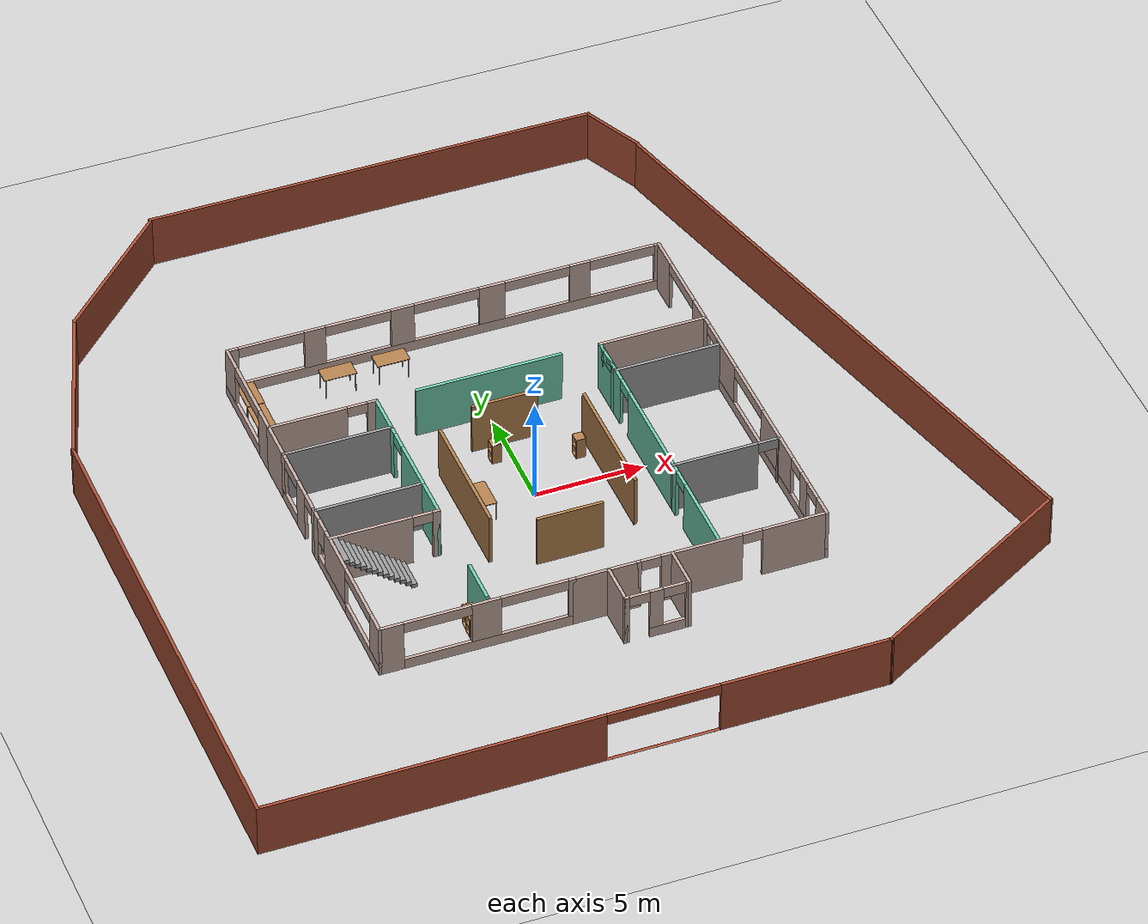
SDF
<sdf version="1.6">
 <world name="default">
  <plugin name="welcomeMessage" filename="libhello.so"/>
  <light name="sun" type="directional">
   <pose>0 0 10 0 -0 0</pose>
   <diffuse>0.8 0.8 0.8 1</diffuse>
   <specular>0.2 0.2 0.2 1</specular>
   <attenuation>
    <range>1000</range>
    <constant>0.9</constant>
    <linear>0.01</linear>
    <quadratic>0.001</quadratic>
   </attenuation>
   <direction>-0.5 0.1 -0.9</direction>
  </light>
  <model name="ground_plane">
   <static>1</static>
   <link name="link">
    <collision name="collision">
     <geometry><plane><normal>0 0 1</normal><size>100 100</size></plane></geometry>
     <surface><friction><ode><mu>100</mu><mu2>50</mu2></ode></friction></surface>
    </collision>
    <visual name="visual">
     <cast_shadows>0</cast_shadows>
     <geometry><plane><normal>0 0 1</normal><size>100 100</size></plane></geometry>
     <material>
      <script><uri>file://media/materials/scripts/gazebo.material</uri><name>Gazebo/Grey</name></script>
     </material>
    </visual>
   </link>
  </model>
  <gravity>0 0 -9.8</gravity>
  <magnetic_field>6e-06 2.3e-05 -4.2e-05</magnetic_field>
  <atmosphere type="adiabatic"/>
  <physics name="default_physics" default="0" type="ode">
   <max_step_size>0.001</max_step_size>
   <real_time_factor>1</real_time_factor>
   <real_time_update_rate>1000</real_time_update_rate>
  </physics>
  <scene><ambient>0.4 0.4 0.4 1</ambient><background>0.7 0.7 0.7 1</background><shadows>1</shadows></scene>
  <spherical_coordinates>
   <surface_model>EARTH_WGS84</surface_model>
   <latitude_deg>0</latitude_deg>
   <longitude_deg>0</longitude_deg>
   <elevation>0</elevation>
   <heading_deg>0</heading_deg>
  </spherical_coordinates>
  <model name="buildingv2">
   <pose>0.458303 2.11352 0 0 -0 0</pose>
   <link name="Stairs_1">
    <visual name="Stairs_1_Visual_0">
     <pose>-7.25739 -4.97699 0.096154 0 0 -1.5708</pose>
     <geometry><box><size>1.5 0.246923 0.192308</size></box></geometry>
     <material>
      <script><uri>file://media/materials/scripts/gazebo.material</uri><name>Gazebo/Grey</name></script>
      <ambient>1 1 1 1</ambient>
     </material>
     <meta><layer>0</layer></meta>
    </visual>
    <collision name="Stairs_1_Collision_0">
     <geometry><box><size>1.5 0.246923 0.192308</size></box></geometry>
     <pose>-7.25739 -4.97699 0.096154 0 0 -1.5708</pose>
    </collision>
    <visual name="Stairs_1_Visual_1">
     <pose>-7.50432 -4.97699 0.288462 0 0 -1.5708</pose>
     <geometry><box><size>1.5 0.246923 0.192308</size></box></geometry>
     <material>
      <script><uri>file://media/materials/scripts/gazebo.material</uri><name>Gazebo/Grey</name></script>
      <ambient>1 1 1 1</ambient>
     </material>
     <meta><layer>0</layer></meta>
    </visual>
    <collision name="Stairs_1_Collision_1">
     <geometry><box><size>1.5 0.246923 0.192308</size></box></geometry>
     <pose>-7.50432 -4.97699 0.288462 0 0 -1.5708</pose>
    </collision>
    <visual name="Stairs_1_Visual_2">
     <pose>-7.75124 -4.97699 0.480769 0 0 -1.5708</pose>
     <geometry><box><size>1.5 0.246923 0.192308</size></box></geometry>
     <material>
      <script><uri>file://media/materials/scripts/gazebo.material</uri><name>Gazebo/Grey</name></script>
      <ambient>1 1 1 1</ambient>
     </material>
     <meta><layer>0</layer></meta>
    </visual>
    <collision name="Stairs_1_Collision_2">
     <geometry><box><size>1.5 0.246923 0.192308</size></box></geometry>
     <pose>-7.75124 -4.97699 0.480769 0 0 -1.5708</pose>
    </collision>
    <visual name="Stairs_1_Visual_3">
     <pose>-7.99816 -4.97699 0.673077 0 0 -1.5708</pose>
     <geometry><box><size>1.5 0.246923 0.192308</size></box></geometry>
     <material>
      <script><uri>file://media/materials/scripts/gazebo.material</uri><name>Gazebo/Grey</name></script>
      <ambient>1 1 1 1</ambient>
     </material>
     <meta><layer>0</layer></meta>
    </visual>
    <collision name="Stairs_1_Collision_3">
     <geometry><box><size>1.5 0.246923 0.192308</size></box></geometry>
     <pose>-7.99816 -4.97699 0.673077 0 0 -1.5708</pose>
    </collision>
    <visual name="Stairs_1_Visual_4">
     <pose>-8.24509 -4.97699 0.865385 0 0 -1.5708</pose>
     <geometry><box><size>1.5 0.246923 0.192308</size></box></geometry>
     <material>
      <script><uri>file://media/materials/scripts/gazebo.material</uri><name>Gazebo/Grey</name></script>
      <ambient>1 1 1 1</ambient>
     </material>
     <meta><layer>0</layer></meta>
    </visual>
    <collision name="Stairs_1_Collision_4">
     <geometry><box><size>1.5 0.246923 0.192308</size></box></geometry>
     <pose>-8.24509 -4.97699 0.865385 0 0 -1.5708</pose>
    </collision>
    <visual name="Stairs_1_Visual_5">
     <pose>-8.49201 -4.97699 1.05769 0 0 -1.5708</pose>
     <geometry><box><size>1.5 0.246923 0.192308</size></box></geometry>
     <material>
      <script><uri>file://media/materials/scripts/gazebo.material</uri><name>Gazebo/Grey</name></script>
      <ambient>1 1 1 1</ambient>
     </material>
     <meta><layer>0</layer></meta>
    </visual>
    <collision name="Stairs_1_Collision_5">
     <geometry><box><size>1.5 0.246923 0.192308</size></box></geometry>
     <pose>-8.49201 -4.97699 1.05769 0 0 -1.5708</pose>
    </collision>
    <visual name="Stairs_1_Visual_6">
     <pose>-8.73893 -4.97699 1.25 0 0 -1.5708</pose>
     <geometry><box><size>1.5 0.246923 0.192308</size></box></geometry>
     <material>
      <script><uri>file://media/materials/scripts/gazebo.material</uri><name>Gazebo/Grey</name></script>
      <ambient>1 1 1 1</ambient>
     </material>
     <meta><layer>0</layer></meta>
    </visual>
    <collision name="Stairs_1_Collision_6">
     <geometry><box><size>1.5 0.246923 0.192308</size></box></geometry>
     <pose>-8.73893 -4.97699 1.25 0 0 -1.5708</pose>
    </collision>
    <visual name="Stairs_1_Visual_7">
     <pose>-8.98586 -4.97699 1.44231 0 0 -1.5708</pose>
     <geometry><box><size>1.5 0.246923 0.192308</size></box></geometry>
     <material>
      <script><uri>file://media/materials/scripts/gazebo.material</uri><name>Gazebo/Grey</name></script>
      <ambient>1 1 1 1</ambient>
     </material>
     <meta><layer>0</layer></meta>
    </visual>
    <collision name="Stairs_1_Collision_7">
     <geometry><box><size>1.5 0.246923 0.192308</size></box></geometry>
     <pose>-8.98586 -4.97699 1.44231 0 0 -1.5708</pose>
    </collision>
    <visual name="Stairs_1_Visual_8">
     <pose>-9.23278 -4.97699 1.63461 0 0 -1.5708</pose>
     <geometry><box><size>1.5 0.246923 0.192308</size></box></geometry>
     <material>
      <script><uri>file://media/materials/scripts/gazebo.material</uri><name>Gazebo/Grey</name></script>
      <ambient>1 1 1 1</ambient>
     </material>
     <meta><layer>0</layer></meta>
    </visual>
    <collision name="Stairs_1_Collision_8">
     <geometry><box><size>1.5 0.246923 0.192308</size></box></geometry>
     <pose>-9.23278 -4.97699 1.63461 0 0 -1.5708</pose>
    </collision>
    <visual name="Stairs_1_Visual_9">
     <pose>-9.4797 -4.97699 1.82692 0 0 -1.5708</pose>
     <geometry><box><size>1.5 0.246923 0.192308</size></box></geometry>
     <material>
      <script><uri>file://media/materials/scripts/gazebo.material</uri><name>Gazebo/Grey</name></script>
      <ambient>1 1 1 1</ambient>
     </material>
     <meta><layer>0</layer></meta>
    </visual>
    <collision name="Stairs_1_Collision_9">
     <geometry><box><size>1.5 0.246923 0.192308</size></box></geometry>
     <pose>-9.4797 -4.97699 1.82692 0 0 -1.5708</pose>
    </collision>
    <visual name="Stairs_1_Visual_10">
     <pose>-9.72662 -4.97699 2.01923 0 0 -1.5708</pose>
     <geometry><box><size>1.5 0.246923 0.192308</size></box></geometry>
     <material>
      <script><uri>file://media/materials/scripts/gazebo.material</uri><name>Gazebo/Grey</name></script>
      <ambient>1 1 1 1</ambient>
     </material>
     <meta><layer>0</layer></meta>
    </visual>
    <collision name="Stairs_1_Collision_10">
     <geometry><box><size>1.5 0.246923 0.192308</size></box></geometry>
     <pose>-9.72662 -4.97699 2.01923 0 0 -1.5708</pose>
    </collision>
    <visual name="Stairs_1_Visual_11">
     <pose>-9.97355 -4.97699 2.21154 0 0 -1.5708</pose>
     <geometry><box><size>1.5 0.246923 0.192308</size></box></geometry>
     <material>
      <script><uri>file://media/materials/scripts/gazebo.material</uri><name>Gazebo/Grey</name></script>
      <ambient>1 1 1 1</ambient>
     </material>
     <meta><layer>0</layer></meta>
    </visual>
    <collision name="Stairs_1_Collision_11">
     <geometry><box><size>1.5 0.246923 0.192308</size></box></geometry>
     <pose>-9.97355 -4.97699 2.21154 0 0 -1.5708</pose>
    </collision>
    <visual name="Stairs_1_Visual_12">
     <pose>-10.2205 -4.97699 2.40385 0 0 -1.5708</pose>
     <geometry><box><size>1.5 0.246923 0.192308</size></box></geometry>
     <material>
      <script><uri>file://media/materials/scripts/gazebo.material</uri><name>Gazebo/Grey</name></script>
      <ambient>1 1 1 1</ambient>
     </material>
     <meta><layer>0</layer></meta>
    </visual>
    <collision name="Stairs_1_Collision_12">
     <geometry><box><size>1.5 0.246923 0.192308</size></box></geometry>
     <pose>-10.2205 -4.97699 2.40385 0 0 -1.5708</pose>
    </collision>
   </link>
   <link name="Wall_102">
    <collision name="Wall_102_Collision">
     <geometry><box><size>7.5 0.15 2.5</size></box></geometry>
     <pose>0 0 1.25 0 -0 0</pose>
    </collision>
    <visual name="Wall_102_Visual">
     <pose>0 0 1.25 0 -0 0</pose>
     <geometry><box><size>7.5 0.15 2.5</size></box></geometry>
     <material>
      <script><uri>file://media/materials/scripts/gazebo.material</uri><name>Gazebo/Bricks</name></script>
      <ambient>1 1 1 1</ambient>
     </material>
     <meta><layer>0</layer></meta>
    </visual>
    <pose>-13.3137 15.568 0 0 0 -2.35619</pose>
   </link>
   <link name="Wall_103">
    <collision name="Wall_103_Collision">
     <geometry><box><size>8.52644 0.15 2.5</size></box></geometry>
     <pose>0 0 1.25 0 -0 0</pose>
    </collision>
    <visual name="Wall_103_Visual">
     <pose>0 0 1.25 0 -0 0</pose>
     <geometry><box><size>8.52644 0.15 2.5</size></box></geometry>
     <material>
      <script><uri>file://media/materials/scripts/gazebo.material</uri><name>Gazebo/Bricks</name></script>
      <ambient>1 1 1 1</ambient>
     </material>
     <meta><layer>0</layer></meta>
    </visual>
    <pose>-17.2612 9.00429 0 0 0 -1.89871</pose>
   </link>
   <link name="Wall_104">
    <collision name="Wall_104_Collision">
     <geometry><box><size>23.5 0.15 2.5</size></box></geometry>
     <pose>0 0 1.25 0 -0 0</pose>
    </collision>
    <visual name="Wall_104_Visual">
     <pose>0 0 1.25 0 -0 0</pose>
     <geometry><box><size>23.5 0.15 2.5</size></box></geometry>
     <material>
      <script><uri>file://media/materials/scripts/gazebo.material</uri><name>Gazebo/Bricks</name></script>
      <ambient>1 1 1 1</ambient>
     </material>
     <meta><layer>0</layer></meta>
    </visual>
    <pose>-18.6101 -6.63577 0 0 0 -1.5708</pose>
   </link>
   <link name="Wall_105">
    <pose>-4.81009 -18.3108 0 0 -0 0</pose>
    <visual name="Wall_105_Visual_0">
     <pose>-6.33047 0 1.25 0 -0 0</pose>
     <geometry><box><size>15.0891 0.15 2.5</size></box></geometry>
     <material>
      <script><uri>file://media/materials/scripts/gazebo.material</uri><name>Gazebo/Bricks</name></script>
      <ambient>1 1 1 1</ambient>
     </material>
     <meta><layer>0</layer></meta>
    </visual>
    <collision name="Wall_105_Collision_0">
     <geometry><box><size>15.0891 0.15 2.5</size></box></geometry>
     <pose>-6.33047 0 1.25 0 -0 0</pose>
    </collision>
    <visual name="Wall_105_Visual_1">
     <pose>7.54453 0 0.00075 0 -0 0</pose>
     <geometry><box><size>12.6609 0.15 0.0015</size></box></geometry>
     <material>
      <script><uri>file://media/materials/scripts/gazebo.material</uri><name>Gazebo/Bricks</name></script>
      <ambient>1 1 1 1</ambient>
     </material>
     <meta><layer>0</layer></meta>
    </visual>
    <collision name="Wall_105_Collision_1">
     <geometry><box><size>12.6609 0.15 0.0015</size></box></geometry>
     <pose>7.54453 0 0.00075 0 -0 0</pose>
    </collision>
    <visual name="Wall_105_Visual_2">
     <pose>10.0445 0 1.25075 0 -0 0</pose>
     <geometry><box><size>7.66093 0.15 2.4985</size></box></geometry>
     <material>
      <script><uri>file://media/materials/scripts/gazebo.material</uri><name>Gazebo/Bricks</name></script>
      <ambient>1 1 1 1</ambient>
     </material>
     <meta><layer>0</layer></meta>
    </visual>
    <collision name="Wall_105_Collision_2">
     <geometry><box><size>7.66093 0.15 2.4985</size></box></geometry>
     <pose>10.0445 0 1.25075 0 -0 0</pose>
    </collision>
    <visual name="Wall_105_Visual_3">
     <pose>3.71407 0 2.25075 0 -0 0</pose>
     <geometry><box><size>5 0.15 0.4985</size></box></geometry>
     <material>
      <script><uri>file://media/materials/scripts/gazebo.material</uri><name>Gazebo/Bricks</name></script>
      <ambient>1 1 1 1</ambient>
     </material>
     <meta><layer>0</layer></meta>
    </visual>
    <collision name="Wall_105_Collision_3">
     <geometry><box><size>5 0.15 0.4985</size></box></geometry>
     <pose>3.71407 0 2.25075 0 -0 0</pose>
    </collision>
   </link>
   <link name="Wall_106">
    <collision name="Wall_106_Collision">
     <geometry><box><size>11.25 0.15 2.5</size></box></geometry>
     <pose>0 0 1.25 0 -0 0</pose>
    </collision>
    <visual name="Wall_106_Visual">
     <pose>0 0 1.25 0 -0 0</pose>
     <geometry><box><size>11.25 0.15 2.5</size></box></geometry>
     <material>
      <script><uri>file://media/materials/scripts/gazebo.material</uri><name>Gazebo/Bricks</name></script>
      <ambient>1 1 1 1</ambient>
     </material>
     <meta><layer>0</layer></meta>
    </visual>
    <pose>13.7964 -15.5358 0 0 -0 0.523599</pose>
   </link>
   <link name="Wall_107">
    <collision name="Wall_107_Collision">
     <geometry><box><size>29.3218 0.15 2.5</size></box></geometry>
     <pose>0 0 1.25 0 -0 0</pose>
    </collision>
    <visual name="Wall_107_Visual">
     <pose>0 0 1.25 0 -0 0</pose>
     <geometry><box><size>29.3218 0.15 2.5</size></box></geometry>
     <material>
      <script><uri>file://media/materials/scripts/gazebo.material</uri><name>Gazebo/Bricks</name></script>
      <ambient>1 1 1 1</ambient>
     </material>
     <meta><layer>0</layer></meta>
    </visual>
    <pose>14.9208 1.35275 0 0 -0 1.82599</pose>
   </link>
   <link name="Wall_108">
    <collision name="Wall_108_Collision">
     <geometry><box><size>3.15356 0.15 2.5</size></box></geometry>
     <pose>0 0 1.25 0 -0 0</pose>
    </collision>
    <visual name="Wall_108_Visual">
     <pose>0 0 1.25 0 -0 0</pose>
     <geometry><box><size>3.15356 0.15 2.5</size></box></geometry>
     <material>
      <script><uri>file://media/materials/scripts/gazebo.material</uri><name>Gazebo/Bricks</name></script>
      <ambient>1 1 1 1</ambient>
     </material>
     <meta><layer>0</layer></meta>
    </visual>
    <pose>10.6056 16.9518 0 0 -0 2.006</pose>
   </link>
   <link name="Wall_109">
    <collision name="Wall_109_Collision">
     <geometry><box><size>20.75 0.15 2.5</size></box></geometry>
     <pose>0 0 1.25 0 -0 0</pose>
    </collision>
    <visual name="Wall_109_Visual">
     <pose>0 0 1.25 0 -0 0</pose>
     <geometry><box><size>20.75 0.15 2.5</size></box></geometry>
     <material>
      <script><uri>file://media/materials/scripts/gazebo.material</uri><name>Gazebo/Bricks</name></script>
      <ambient>1 1 1 1</ambient>
     </material>
     <meta><layer>0</layer></meta>
    </visual>
    <pose>-0.327523 18.3136 0 0 -0 3.14159</pose>
   </link>
   <link name="Wall_111">
    <collision name="Wall_111_Collision">
     <geometry><box><size>2 0.15 2.5</size></box></geometry>
     <pose>0 0 1.25 0 -0 0</pose>
    </collision>
    <visual name="Wall_111_Visual">
     <pose>0 0 1.25 0 -0 0</pose>
     <geometry><box><size>2 0.15 2.5</size></box></geometry>
     <material>
      <script><uri>file://media/materials/scripts/gazebo.material</uri><name>Gazebo/Grey</name></script>
      <ambient>0.435294 0.796078 0.67451 1</ambient>
     </material>
     <meta><layer>0</layer></meta>
    </visual>
    <pose>4.67372 2.45158 0 0 -0 1.5708</pose>
   </link>
   <link name="Wall_112">
    <collision name="Wall_112_Collision">
     <geometry><box><size>5 0.15 2.5</size></box></geometry>
     <pose>0 0 1.25 0 -0 0</pose>
    </collision>
    <visual name="Wall_112_Visual">
     <pose>0 0 1.25 0 -0 0</pose>
     <geometry><box><size>5 0.15 2.5</size></box></geometry>
     <material>
      <script><uri>file://media/materials/scripts/gazebo.material</uri><name>Gazebo/Grey</name></script>
      <ambient>0.760784 0.662745 0.627451 1</ambient>
     </material>
     <meta><layer>0</layer></meta>
    </visual>
    <pose>7.09872 3.37658 0 0 -0 0</pose>
   </link>
   <link name="Wall_121">
    <pose>9.52372 6.05158 0 0 -0 1.5708</pose>
    <visual name="Wall_121_Visual_0">
     <pose>-2.0984 0 1.25 0 -0 0</pose>
     <geometry><box><size>1.3032 0.15 2.5</size></box></geometry>
     <material>
      <script><uri>file://media/materials/scripts/gazebo.material</uri><name>Gazebo/Grey</name></script>
      <ambient>0.760784 0.662745 0.627451 1</ambient>
     </material>
     <meta><layer>0</layer></meta>
    </visual>
    <collision name="Wall_121_Collision_0">
     <geometry><box><size>1.3032 0.15 2.5</size></box></geometry>
     <pose>-2.0984 0 1.25 0 -0 0</pose>
    </collision>
    <visual name="Wall_121_Visual_1">
     <pose>1.9816 0 1.25 0 -0 0</pose>
     <geometry><box><size>1.5368 0.15 2.5</size></box></geometry>
     <material>
      <script><uri>file://media/materials/scripts/gazebo.material</uri><name>Gazebo/Grey</name></script>
      <ambient>0.760784 0.662745 0.627451 1</ambient>
     </material>
     <meta><layer>0</layer></meta>
    </visual>
    <collision name="Wall_121_Collision_1">
     <geometry><box><size>1.5368 0.15 2.5</size></box></geometry>
     <pose>1.9816 0 1.25 0 -0 0</pose>
    </collision>
    <visual name="Wall_121_Visual_2">
     <pose>-0.116804 0 2.25 0 -0 0</pose>
     <geometry><box><size>2.66 0.15 0.5</size></box></geometry>
     <material>
      <script><uri>file://media/materials/scripts/gazebo.material</uri><name>Gazebo/Grey</name></script>
      <ambient>0.760784 0.662745 0.627451 1</ambient>
     </material>
     <meta><layer>0</layer></meta>
    </visual>
    <collision name="Wall_121_Collision_2">
     <geometry><box><size>2.66 0.15 0.5</size></box></geometry>
     <pose>-0.116804 0 2.25 0 -0 0</pose>
    </collision>
   </link>
   <link name="Wall_123">
    <pose>9.52372 -3.39842 0 0 0 -1.5708</pose>
    <visual name="Wall_123_Visual_0">
     <pose>-6.5741 0 1.25 0 -0 0</pose>
     <geometry><box><size>0.551797 0.15 2.5</size></box></geometry>
     <material>
      <script><uri>file://media/materials/scripts/gazebo.material</uri><name>Gazebo/Grey</name></script>
      <ambient>0.760784 0.662745 0.627451 1</ambient>
     </material>
     <meta><layer>0</layer></meta>
    </visual>
    <collision name="Wall_123_Collision_0">
     <geometry><box><size>0.551797 0.15 2.5</size></box></geometry>
     <pose>-6.5741 0 1.25 0 -0 0</pose>
    </collision>
    <visual name="Wall_123_Visual_1">
     <pose>0.275898 0 0.25 0 -0 0</pose>
     <geometry><box><size>13.1482 0.15 0.5</size></box></geometry>
     <material>
      <script><uri>file://media/materials/scripts/gazebo.material</uri><name>Gazebo/Grey</name></script>
      <ambient>0.760784 0.662745 0.627451 1</ambient>
     </material>
     <meta><layer>0</layer></meta>
    </visual>
    <collision name="Wall_123_Collision_1">
     <geometry><box><size>13.1482 0.15 0.5</size></box></geometry>
     <pose>0.275898 0 0.25 0 -0 0</pose>
    </collision>
    <visual name="Wall_123_Visual_2">
     <pose>-4.26781 0 1.5 0 -0 0</pose>
     <geometry><box><size>2.06079 0.15 2</size></box></geometry>
     <material>
      <script><uri>file://media/materials/scripts/gazebo.material</uri><name>Gazebo/Grey</name></script>
      <ambient>0.760784 0.662745 0.627451 1</ambient>
     </material>
     <meta><layer>0</layer></meta>
    </visual>
    <collision name="Wall_123_Collision_2">
     <geometry><box><size>2.06079 0.15 2</size></box></geometry>
     <pose>-4.26781 0 1.5 0 -0 0</pose>
    </collision>
    <visual name="Wall_123_Visual_3">
     <pose>1.4125 0 1.5 0 -0 0</pose>
     <geometry><box><size>3.29982 0.15 2</size></box></geometry>
     <material>
      <script><uri>file://media/materials/scripts/gazebo.material</uri><name>Gazebo/Grey</name></script>
      <ambient>0.760784 0.662745 0.627451 1</ambient>
     </material>
     <meta><layer>0</layer></meta>
    </visual>
    <collision name="Wall_123_Collision_3">
     <geometry><box><size>3.29982 0.15 2</size></box></geometry>
     <pose>1.4125 0 1.5 0 -0 0</pose>
    </collision>
    <visual name="Wall_123_Visual_4">
     <pose>4.41893 0 1.5 0 -0 0</pose>
     <geometry><box><size>0.713053 0.15 2</size></box></geometry>
     <material>
      <script><uri>file://media/materials/scripts/gazebo.material</uri><name>Gazebo/Grey</name></script>
      <ambient>0.760784 0.662745 0.627451 1</ambient>
     </material>
     <meta><layer>0</layer></meta>
    </visual>
    <collision name="Wall_123_Collision_4">
     <geometry><box><size>0.713053 0.15 2</size></box></geometry>
     <pose>4.41893 0 1.5 0 -0 0</pose>
    </collision>
    <visual name="Wall_123_Visual_5">
     <pose>6.31273 0 1.5 0 -0 0</pose>
     <geometry><box><size>1.07454 0.15 2</size></box></geometry>
     <material>
      <script><uri>file://media/materials/scripts/gazebo.material</uri><name>Gazebo/Grey</name></script>
      <ambient>0.760784 0.662745 0.627451 1</ambient>
     </material>
     <meta><layer>0</layer></meta>
    </visual>
    <collision name="Wall_123_Collision_5">
     <geometry><box><size>1.07454 0.15 2</size></box></geometry>
     <pose>6.31273 0 1.5 0 -0 0</pose>
    </collision>
    <visual name="Wall_123_Visual_6">
     <pose>-5.7982 0 2.25 0 -0 0</pose>
     <geometry><box><size>1 0.15 0.5</size></box></geometry>
     <material>
      <script><uri>file://media/materials/scripts/gazebo.material</uri><name>Gazebo/Grey</name></script>
      <ambient>0.760784 0.662745 0.627451 1</ambient>
     </material>
     <meta><layer>0</layer></meta>
    </visual>
    <collision name="Wall_123_Collision_6">
     <geometry><box><size>1 0.15 0.5</size></box></geometry>
     <pose>-5.7982 0 2.25 0 -0 0</pose>
    </collision>
    <visual name="Wall_123_Visual_7">
     <pose>-1.73742 0 2.25 0 -0 0</pose>
     <geometry><box><size>3 0.15 0.5</size></box></geometry>
     <material>
      <script><uri>file://media/materials/scripts/gazebo.material</uri><name>Gazebo/Grey</name></script>
      <ambient>0.760784 0.662745 0.627451 1</ambient>
     </material>
     <meta><layer>0</layer></meta>
    </visual>
    <collision name="Wall_123_Collision_7">
     <geometry><box><size>3 0.15 0.5</size></box></geometry>
     <pose>-1.73742 0 2.25 0 -0 0</pose>
    </collision>
    <visual name="Wall_123_Visual_8">
     <pose>3.56241 0 2.25 0 -0 0</pose>
     <geometry><box><size>1 0.15 0.5</size></box></geometry>
     <material>
      <script><uri>file://media/materials/scripts/gazebo.material</uri><name>Gazebo/Grey</name></script>
      <ambient>0.760784 0.662745 0.627451 1</ambient>
     </material>
     <meta><layer>0</layer></meta>
    </visual>
    <collision name="Wall_123_Collision_8">
     <geometry><box><size>1 0.15 0.5</size></box></geometry>
     <pose>3.56241 0 2.25 0 -0 0</pose>
    </collision>
    <visual name="Wall_123_Visual_9">
     <pose>5.27546 0 2.25 0 -0 0</pose>
     <geometry><box><size>1 0.15 0.5</size></box></geometry>
     <material>
      <script><uri>file://media/materials/scripts/gazebo.material</uri><name>Gazebo/Grey</name></script>
      <ambient>0.760784 0.662745 0.627451 1</ambient>
     </material>
     <meta><layer>0</layer></meta>
    </visual>
    <collision name="Wall_123_Collision_9">
     <geometry><box><size>1 0.15 0.5</size></box></geometry>
     <pose>5.27546 0 2.25 0 -0 0</pose>
    </collision>
   </link>
   <link name="Wall_129">
    <pose>4.67372 -7.55852 0 0 0 -1.5708</pose>
    <visual name="Wall_129_Visual_0">
     <pose>-2.29898 0 1.25 0 -0 0</pose>
     <geometry><box><size>0.481835 0.15 2.5</size></box></geometry>
     <material>
      <script><uri>file://media/materials/scripts/gazebo.material</uri><name>Gazebo/Grey</name></script>
      <ambient>0.435294 0.796078 0.67451 1</ambient>
     </material>
     <meta><layer>0</layer></meta>
    </visual>
    <collision name="Wall_129_Collision_0">
     <geometry><box><size>0.481835 0.15 2.5</size></box></geometry>
     <pose>-2.29898 0 1.25 0 -0 0</pose>
    </collision>
    <visual name="Wall_129_Visual_1">
     <pose>0.690917 0 1.25 0 -0 0</pose>
     <geometry><box><size>3.69797 0.15 2.5</size></box></geometry>
     <material>
      <script><uri>file://media/materials/scripts/gazebo.material</uri><name>Gazebo/Grey</name></script>
      <ambient>0.435294 0.796078 0.67451 1</ambient>
     </material>
     <meta><layer>0</layer></meta>
    </visual>
    <collision name="Wall_129_Collision_1">
     <geometry><box><size>3.69797 0.15 2.5</size></box></geometry>
     <pose>0.690917 0 1.25 0 -0 0</pose>
    </collision>
    <visual name="Wall_129_Visual_2">
     <pose>-1.60807 0 2.25 0 -0 0</pose>
     <geometry><box><size>0.9 0.15 0.5</size></box></geometry>
     <material>
      <script><uri>file://media/materials/scripts/gazebo.material</uri><name>Gazebo/Grey</name></script>
      <ambient>0.435294 0.796078 0.67451 1</ambient>
     </material>
     <meta><layer>0</layer></meta>
    </visual>
    <collision name="Wall_129_Collision_2">
     <geometry><box><size>0.9 0.15 0.5</size></box></geometry>
     <pose>-1.60807 0 2.25 0 -0 0</pose>
    </collision>
   </link>
   <link name="Wall_131">
    <pose>4.67372 -1.78352 0 0 -0 1.5708</pose>
    <visual name="Wall_131_Visual_0">
     <pose>-0.819633 0 1.25 0 -0 0</pose>
     <geometry><box><size>5.13093 0.15 2.5</size></box></geometry>
     <material>
      <script><uri>file://media/materials/scripts/gazebo.material</uri><name>Gazebo/Grey</name></script>
      <ambient>0.435294 0.796078 0.67451 1</ambient>
     </material>
     <meta><layer>0</layer></meta>
    </visual>
    <collision name="Wall_131_Collision_0">
     <geometry><box><size>5.13093 0.15 2.5</size></box></geometry>
     <pose>-0.819633 0 1.25 0 -0 0</pose>
    </collision>
    <visual name="Wall_131_Visual_1">
     <pose>3.01547 0 1.25 0 -0 0</pose>
     <geometry><box><size>0.739267 0.15 2.5</size></box></geometry>
     <material>
      <script><uri>file://media/materials/scripts/gazebo.material</uri><name>Gazebo/Grey</name></script>
      <ambient>0.435294 0.796078 0.67451 1</ambient>
     </material>
     <meta><layer>0</layer></meta>
    </visual>
    <collision name="Wall_131_Collision_1">
     <geometry><box><size>0.739267 0.15 2.5</size></box></geometry>
     <pose>3.01547 0 1.25 0 -0 0</pose>
    </collision>
    <visual name="Wall_131_Visual_2">
     <pose>2.19583 0 2.25 0 -0 0</pose>
     <geometry><box><size>0.9 0.15 0.5</size></box></geometry>
     <material>
      <script><uri>file://media/materials/scripts/gazebo.material</uri><name>Gazebo/Grey</name></script>
      <ambient>0.435294 0.796078 0.67451 1</ambient>
     </material>
     <meta><layer>0</layer></meta>
    </visual>
    <collision name="Wall_131_Collision_2">
     <geometry><box><size>0.9 0.15 0.5</size></box></geometry>
     <pose>2.19583 0 2.25 0 -0 0</pose>
    </collision>
   </link>
   <link name="Wall_133">
    <pose>7.09872 -5.06702 0 0 -0 0</pose>
    <visual name="Wall_133_Visual_0">
     <pose>-0.542322 0 1.25 0 -0 0</pose>
     <geometry><box><size>3.91535 0.15 2.5</size></box></geometry>
     <material>
      <script><uri>file://media/materials/scripts/gazebo.material</uri><name>Gazebo/Grey</name></script>
      <ambient>1 1 1 1</ambient>
     </material>
     <meta><layer>0</layer></meta>
    </visual>
    <collision name="Wall_133_Collision_0">
     <geometry><box><size>3.91535 0.15 2.5</size></box></geometry>
     <pose>-0.542322 0 1.25 0 -0 0</pose>
    </collision>
    <visual name="Wall_133_Visual_1">
     <pose>2.40768 0 1.25 0 -0 0</pose>
     <geometry><box><size>0.184645 0.15 2.5</size></box></geometry>
     <material>
      <script><uri>file://media/materials/scripts/gazebo.material</uri><name>Gazebo/Grey</name></script>
      <ambient>1 1 1 1</ambient>
     </material>
     <meta><layer>0</layer></meta>
    </visual>
    <collision name="Wall_133_Collision_1">
     <geometry><box><size>0.184645 0.15 2.5</size></box></geometry>
     <pose>2.40768 0 1.25 0 -0 0</pose>
    </collision>
    <visual name="Wall_133_Visual_2">
     <pose>1.86536 0 2.25 0 -0 0</pose>
     <geometry><box><size>0.9 0.15 0.5</size></box></geometry>
     <material>
      <script><uri>file://media/materials/scripts/gazebo.material</uri><name>Gazebo/Grey</name></script>
      <ambient>1 1 1 1</ambient>
     </material>
     <meta><layer>0</layer></meta>
    </visual>
    <collision name="Wall_133_Collision_2">
     <geometry><box><size>0.9 0.15 0.5</size></box></geometry>
     <pose>1.86536 0 2.25 0 -0 0</pose>
    </collision>
   </link>
   <link name="Wall_143">
    <collision name="Wall_143_Collision">
     <geometry><box><size>3 0.15 2.5</size></box></geometry>
     <pose>0 0 1.25 0 -0 0</pose>
    </collision>
    <visual name="Wall_143_Visual">
     <pose>0 0 1.25 0 -0 0</pose>
     <geometry><box><size>3 0.15 2.5</size></box></geometry>
     <material>
      <script><uri>file://media/materials/scripts/gazebo.material</uri><name>Gazebo/Wood</name></script>
      <ambient>1 1 1 1</ambient>
     </material>
     <meta><layer>0</layer></meta>
    </visual>
    <pose>-0.451279 1.52658 0 0 -0 0</pose>
   </link>
   <link name="Wall_153">
    <collision name="Wall_153_Collision">
     <geometry><box><size>2.25 0.15 2.5</size></box></geometry>
     <pose>0 0 1.25 0 -0 0</pose>
    </collision>
    <visual name="Wall_153_Visual">
     <pose>0 0 1.25 0 -0 0</pose>
     <geometry><box><size>2.25 0.15 2.5</size></box></geometry>
     <material>
      <script><uri>file://media/materials/scripts/gazebo.material</uri><name>Gazebo/Grey</name></script>
      <ambient>0.435294 0.796078 0.67451 1</ambient>
     </material>
     <meta><layer>0</layer></meta>
    </visual>
    <pose>-5.57628 -8.92342 0 0 0 -1.5708</pose>
   </link>
   <link name="Wall_154">
    <collision name="Wall_154_Collision">
     <geometry><box><size>0.25 0.15 2.5</size></box></geometry>
     <pose>0 0 1.25 0 -0 0</pose>
    </collision>
    <visual name="Wall_154_Visual">
     <pose>0 0 1.25 0 -0 0</pose>
     <geometry><box><size>0.25 0.15 2.5</size></box></geometry>
     <material>
      <script><uri>file://media/materials/scripts/gazebo.material</uri><name>Gazebo/Grey</name></script>
      <ambient>1 1 1 1</ambient>
     </material>
     <meta><layer>0</layer></meta>
    </visual>
    <pose>-5.57628 -10.0234 0 0 0 -1.5708</pose>
   </link>
   <link name="Wall_159">
    <collision name="Wall_159_Collision">
     <geometry><box><size>6.7 0.15 2.5</size></box></geometry>
     <pose>0 0 1.25 0 -0 0</pose>
    </collision>
    <visual name="Wall_159_Visual">
     <pose>0 0 1.25 0 -0 0</pose>
     <geometry><box><size>6.7 0.15 2.5</size></box></geometry>
     <material>
      <script><uri>file://media/materials/scripts/gazebo.material</uri><name>Gazebo/Grey</name></script>
      <ambient>0.435294 0.796078 0.67451 1</ambient>
     </material>
     <meta><layer>0</layer></meta>
    </visual>
    <pose>-0.451279 3.37658 0 0 -0 3.14159</pose>
   </link>
   <link name="Wall_165">
    <collision name="Wall_165_Collision">
     <geometry><box><size>2 0.15 2.5</size></box></geometry>
     <pose>0 0 1.25 0 -0 0</pose>
    </collision>
    <visual name="Wall_165_Visual">
     <pose>0 0 1.25 0 -0 0</pose>
     <geometry><box><size>2 0.15 2.5</size></box></geometry>
     <material>
      <script><uri>file://media/materials/scripts/gazebo.material</uri><name>Gazebo/Grey</name></script>
      <ambient>0.760784 0.662745 0.627451 1</ambient>
     </material>
     <meta><layer>0</layer></meta>
    </visual>
    <pose>2.56396 -11.1335 0 0 0 -1.57106</pose>
   </link>
   <link name="Wall_168">
    <pose>1.13872 -12.0584 0 0 -0 3.14159</pose>
    <visual name="Wall_168_Visual_0">
     <pose>-1.37335 0 1.25 0 -0 0</pose>
     <geometry><box><size>0.253306 0.15 2.5</size></box></geometry>
     <material>
      <script><uri>file://media/materials/scripts/gazebo.material</uri><name>Gazebo/Grey</name></script>
      <ambient>0.760784 0.662745 0.627451 1</ambient>
     </material>
     <meta><layer>0</layer></meta>
    </visual>
    <collision name="Wall_168_Collision_0">
     <geometry><box><size>0.253306 0.15 2.5</size></box></geometry>
     <pose>-1.37335 0 1.25 0 -0 0</pose>
    </collision>
    <visual name="Wall_168_Visual_1">
     <pose>1.37958 0 1.25 0 -0 0</pose>
     <geometry><box><size>0.240843 0.15 2.5</size></box></geometry>
     <material>
      <script><uri>file://media/materials/scripts/gazebo.material</uri><name>Gazebo/Grey</name></script>
      <ambient>0.760784 0.662745 0.627451 1</ambient>
     </material>
     <meta><layer>0</layer></meta>
    </visual>
    <collision name="Wall_168_Collision_1">
     <geometry><box><size>0.240843 0.15 2.5</size></box></geometry>
     <pose>1.37958 0 1.25 0 -0 0</pose>
    </collision>
    <visual name="Wall_168_Visual_2">
     <pose>-0.443769 0 0.25 0 -0 0</pose>
     <geometry><box><size>1.60585 0.15 0.5</size></box></geometry>
     <material>
      <script><uri>file://media/materials/scripts/gazebo.material</uri><name>Gazebo/Grey</name></script>
      <ambient>0.760784 0.662745 0.627451 1</ambient>
     </material>
     <meta><layer>0</layer></meta>
    </visual>
    <collision name="Wall_168_Collision_2">
     <geometry><box><size>1.60585 0.15 0.5</size></box></geometry>
     <pose>-0.443769 0 0.25 0 -0 0</pose>
    </collision>
    <visual name="Wall_168_Visual_3">
     <pose>0.056231 0 1.5 0 -0 0</pose>
     <geometry><box><size>0.60585 0.15 2</size></box></geometry>
     <material>
      <script><uri>file://media/materials/scripts/gazebo.material</uri><name>Gazebo/Grey</name></script>
      <ambient>0.760784 0.662745 0.627451 1</ambient>
     </material>
     <meta><layer>0</layer></meta>
    </visual>
    <collision name="Wall_168_Collision_3">
     <geometry><box><size>0.60585 0.15 2</size></box></geometry>
     <pose>0.056231 0 1.5 0 -0 0</pose>
    </collision>
    <visual name="Wall_168_Visual_4">
     <pose>-0.746694 0 2.25 0 -0 0</pose>
     <geometry><box><size>1 0.15 0.5</size></box></geometry>
     <material>
      <script><uri>file://media/materials/scripts/gazebo.material</uri><name>Gazebo/Grey</name></script>
      <ambient>0.760784 0.662745 0.627451 1</ambient>
     </material>
     <meta><layer>0</layer></meta>
    </visual>
    <collision name="Wall_168_Collision_4">
     <geometry><box><size>1 0.15 0.5</size></box></geometry>
     <pose>-0.746694 0 2.25 0 -0 0</pose>
    </collision>
    <visual name="Wall_168_Visual_5">
     <pose>0.809157 0 2.25 0 -0 0</pose>
     <geometry><box><size>0.9 0.15 0.5</size></box></geometry>
     <material>
      <script><uri>file://media/materials/scripts/gazebo.material</uri><name>Gazebo/Grey</name></script>
      <ambient>0.760784 0.662745 0.627451 1</ambient>
     </material>
     <meta><layer>0</layer></meta>
    </visual>
    <collision name="Wall_168_Collision_5">
     <geometry><box><size>0.9 0.15 0.5</size></box></geometry>
     <pose>0.809157 0 2.25 0 -0 0</pose>
    </collision>
   </link>
   <link name="Wall_170">
    <collision name="Wall_170_Collision">
     <geometry><box><size>2 0.15 2.5</size></box></geometry>
     <pose>0 0 1.25 0 -0 0</pose>
    </collision>
    <visual name="Wall_170_Visual">
     <pose>0 0 1.25 0 -0 0</pose>
     <geometry><box><size>2 0.15 2.5</size></box></geometry>
     <material>
      <script><uri>file://media/materials/scripts/gazebo.material</uri><name>Gazebo/Grey</name></script>
      <ambient>0.760784 0.662745 0.627451 1</ambient>
     </material>
     <meta><layer>0</layer></meta>
    </visual>
    <pose>-0.286279 -11.1334 0 0 -0 1.5708</pose>
   </link>
   <link name="Wall_174">
    <pose>4.67372 2.45158 0 0 0 -1.5708</pose>
    <visual name="Wall_174_Visual_0">
     <pose>-0.698273 0 1.25 0 -0 0</pose>
     <geometry><box><size>0.603454 0.15 2.5</size></box></geometry>
     <material>
      <script><uri>file://media/materials/scripts/gazebo.material</uri><name>Gazebo/Grey</name></script>
      <ambient>0.435294 0.796078 0.67451 1</ambient>
     </material>
     <meta><layer>0</layer></meta>
    </visual>
    <collision name="Wall_174_Collision_0">
     <geometry><box><size>0.603454 0.15 2.5</size></box></geometry>
     <pose>-0.698273 0 1.25 0 -0 0</pose>
    </collision>
    <visual name="Wall_174_Visual_1">
     <pose>0.751727 0 1.25 0 -0 0</pose>
     <geometry><box><size>0.496546 0.15 2.5</size></box></geometry>
     <material>
      <script><uri>file://media/materials/scripts/gazebo.material</uri><name>Gazebo/Grey</name></script>
      <ambient>0.435294 0.796078 0.67451 1</ambient>
     </material>
     <meta><layer>0</layer></meta>
    </visual>
    <collision name="Wall_174_Collision_1">
     <geometry><box><size>0.496546 0.15 2.5</size></box></geometry>
     <pose>0.751727 0 1.25 0 -0 0</pose>
    </collision>
    <visual name="Wall_174_Visual_2">
     <pose>0.053454 0 2.25 0 -0 0</pose>
     <geometry><box><size>0.9 0.15 0.5</size></box></geometry>
     <material>
      <script><uri>file://media/materials/scripts/gazebo.material</uri><name>Gazebo/Grey</name></script>
      <ambient>0.435294 0.796078 0.67451 1</ambient>
     </material>
     <meta><layer>0</layer></meta>
    </visual>
    <collision name="Wall_174_Collision_2">
     <geometry><box><size>0.9 0.15 0.5</size></box></geometry>
     <pose>0.053454 0 2.25 0 -0 0</pose>
    </collision>
   </link>
   <link name="Wall_177">
    <collision name="Wall_177_Collision">
     <geometry><box><size>5 0.15 2.5</size></box></geometry>
     <pose>0 0 1.25 0 -0 0</pose>
    </collision>
    <visual name="Wall_177_Visual">
     <pose>0 0 1.25 0 -0 0</pose>
     <geometry><box><size>5 0.15 2.5</size></box></geometry>
     <material>
      <script><uri>file://media/materials/scripts/gazebo.material</uri><name>Gazebo/Grey</name></script>
      <ambient>1 1 1 1</ambient>
     </material>
     <meta><layer>0</layer></meta>
    </visual>
    <pose>7.09872 1.52658 0 0 -0 0</pose>
   </link>
   <link name="Wall_47">
    <collision name="Wall_47_Collision">
     <geometry><box><size>6 0.15 2.5</size></box></geometry>
     <pose>0 0 1.25 0 -0 0</pose>
    </collision>
    <visual name="Wall_47_Visual">
     <pose>0 0 1.25 0 -0 0</pose>
     <geometry><box><size>6 0.15 2.5</size></box></geometry>
     <material>
      <script><uri>file://media/materials/scripts/gazebo.material</uri><name>Gazebo/Wood</name></script>
      <ambient>1 1 1 1</ambient>
     </material>
     <meta><layer>0</layer></meta>
    </visual>
    <pose>-3.72628 -2.39842 0 0 0 -1.5708</pose>
   </link>
   <link name="Wall_5">
    <collision name="Wall_5_Collision">
     <geometry><box><size>6 0.15 2.5</size></box></geometry>
     <pose>0 0 1.25 0 -0 0</pose>
    </collision>
    <visual name="Wall_5_Visual">
     <pose>0 0 1.25 0 -0 0</pose>
     <geometry><box><size>6 0.15 2.5</size></box></geometry>
     <material>
      <script><uri>file://media/materials/scripts/gazebo.material</uri><name>Gazebo/Wood</name></script>
      <ambient>1 1 1 1</ambient>
     </material>
     <meta><layer>0</layer></meta>
    </visual>
    <pose>2.82372 -2.39842 0 0 -0 1.5708</pose>
   </link>
   <link name="Wall_50">
    <collision name="Wall_50_Collision">
     <geometry><box><size>3 0.15 2.5</size></box></geometry>
     <pose>0 0 1.25 0 -0 0</pose>
    </collision>
    <visual name="Wall_50_Visual">
     <pose>0 0 1.25 0 -0 0</pose>
     <geometry><box><size>3 0.15 2.5</size></box></geometry>
     <material>
      <script><uri>file://media/materials/scripts/gazebo.material</uri><name>Gazebo/Wood</name></script>
      <ambient>1 1 1 1</ambient>
     </material>
     <meta><layer>0</layer></meta>
    </visual>
    <pose>-0.451279 -6.17342 0 0 -0 0</pose>
   </link>
   <link name="Wall_53">
    <collision name="Wall_53_Collision">
     <geometry><box><size>2 0.15 2.5</size></box></geometry>
     <pose>0 0 1.25 0 -0 0</pose>
    </collision>
    <visual name="Wall_53_Visual">
     <pose>0 0 1.25 0 -0 0</pose>
     <geometry><box><size>2 0.15 2.5</size></box></geometry>
     <material>
      <script><uri>file://media/materials/scripts/gazebo.material</uri><name>Gazebo/Grey</name></script>
      <ambient>0.435294 0.796078 0.67451 1</ambient>
     </material>
     <meta><layer>0</layer></meta>
    </visual>
    <pose>-5.57628 2.45158 0 0 -0 1.5708</pose>
   </link>
   <link name="Wall_54">
    <pose>-8.00128 3.37658 0 0 -0 3.14159</pose>
    <visual name="Wall_54_Visual_0">
     <pose>-2.2489 0 1.25 0 -0 0</pose>
     <geometry><box><size>0.502202 0.15 2.5</size></box></geometry>
     <material>
      <script><uri>file://media/materials/scripts/gazebo.material</uri><name>Gazebo/Grey</name></script>
      <ambient>0.760784 0.662745 0.627451 1</ambient>
     </material>
     <meta><layer>0</layer></meta>
    </visual>
    <collision name="Wall_54_Collision_0">
     <geometry><box><size>0.502202 0.15 2.5</size></box></geometry>
     <pose>-2.2489 0 1.25 0 -0 0</pose>
    </collision>
    <visual name="Wall_54_Visual_1">
     <pose>0.701101 0 1.25 0 -0 0</pose>
     <geometry><box><size>3.5978 0.15 2.5</size></box></geometry>
     <material>
      <script><uri>file://media/materials/scripts/gazebo.material</uri><name>Gazebo/Grey</name></script>
      <ambient>0.760784 0.662745 0.627451 1</ambient>
     </material>
     <meta><layer>0</layer></meta>
    </visual>
    <collision name="Wall_54_Collision_1">
     <geometry><box><size>3.5978 0.15 2.5</size></box></geometry>
     <pose>0.701101 0 1.25 0 -0 0</pose>
    </collision>
    <visual name="Wall_54_Visual_2">
     <pose>-1.5478 0 2.25 0 -0 0</pose>
     <geometry><box><size>0.9 0.15 0.5</size></box></geometry>
     <material>
      <script><uri>file://media/materials/scripts/gazebo.material</uri><name>Gazebo/Grey</name></script>
      <ambient>0.760784 0.662745 0.627451 1</ambient>
     </material>
     <meta><layer>0</layer></meta>
    </visual>
    <collision name="Wall_54_Collision_2">
     <geometry><box><size>0.9 0.15 0.5</size></box></geometry>
     <pose>-1.5478 0 2.25 0 -0 0</pose>
    </collision>
   </link>
   <link name="Wall_55">
    <collision name="Wall_55_Collision">
     <geometry><box><size>2 0.15 2.5</size></box></geometry>
     <pose>0 0 1.25 0 -0 0</pose>
    </collision>
    <visual name="Wall_55_Visual">
     <pose>0 0 1.25 0 -0 0</pose>
     <geometry><box><size>2 0.15 2.5</size></box></geometry>
     <material>
      <script><uri>file://media/materials/scripts/gazebo.material</uri><name>Gazebo/Grey</name></script>
      <ambient>0.760784 0.662745 0.627451 1</ambient>
     </material>
     <meta><layer>0</layer></meta>
    </visual>
    <pose>-10.4263 2.45158 0 0 0 -1.5708</pose>
   </link>
   <link name="Wall_56">
    <collision name="Wall_56_Collision">
     <geometry><box><size>5 0.15 2.5</size></box></geometry>
     <pose>0 0 1.25 0 -0 0</pose>
    </collision>
    <visual name="Wall_56_Visual">
     <pose>0 0 1.25 0 -0 0</pose>
     <geometry><box><size>5 0.15 2.5</size></box></geometry>
     <material>
      <script><uri>file://media/materials/scripts/gazebo.material</uri><name>Gazebo/Grey</name></script>
      <ambient>1 1 1 1</ambient>
     </material>
     <meta><layer>0</layer></meta>
    </visual>
    <pose>-8.00128 1.52658 0 0 -0 0</pose>
   </link>
   <link name="Wall_57">
    <pose>-5.57628 -0.398423 0 0 0 -1.5708</pose>
    <visual name="Wall_57_Visual_0">
     <pose>-1.72998 0 1.25 0 -0 0</pose>
     <geometry><box><size>0.54004 0.15 2.5</size></box></geometry>
     <material>
      <script><uri>file://media/materials/scripts/gazebo.material</uri><name>Gazebo/Grey</name></script>
      <ambient>0.435294 0.796078 0.67451 1</ambient>
     </material>
     <meta><layer>0</layer></meta>
    </visual>
    <collision name="Wall_57_Collision_0">
     <geometry><box><size>0.54004 0.15 2.5</size></box></geometry>
     <pose>-1.72998 0 1.25 0 -0 0</pose>
    </collision>
    <visual name="Wall_57_Visual_1">
     <pose>0.72002 0 1.25 0 -0 0</pose>
     <geometry><box><size>2.55996 0.15 2.5</size></box></geometry>
     <material>
      <script><uri>file://media/materials/scripts/gazebo.material</uri><name>Gazebo/Grey</name></script>
      <ambient>0.435294 0.796078 0.67451 1</ambient>
     </material>
     <meta><layer>0</layer></meta>
    </visual>
    <collision name="Wall_57_Collision_1">
     <geometry><box><size>2.55996 0.15 2.5</size></box></geometry>
     <pose>0.72002 0 1.25 0 -0 0</pose>
    </collision>
    <visual name="Wall_57_Visual_2">
     <pose>-1.00996 0 2.25 0 -0 0</pose>
     <geometry><box><size>0.9 0.15 0.5</size></box></geometry>
     <material>
      <script><uri>file://media/materials/scripts/gazebo.material</uri><name>Gazebo/Grey</name></script>
      <ambient>0.435294 0.796078 0.67451 1</ambient>
     </material>
     <meta><layer>0</layer></meta>
    </visual>
    <collision name="Wall_57_Collision_2">
     <geometry><box><size>0.9 0.15 0.5</size></box></geometry>
     <pose>-1.00996 0 2.25 0 -0 0</pose>
    </collision>
   </link>
   <link name="Wall_58">
    <collision name="Wall_58_Collision">
     <geometry><box><size>5 0.15 2.5</size></box></geometry>
     <pose>0 0 1.25 0 -0 0</pose>
    </collision>
    <visual name="Wall_58_Visual">
     <pose>0 0 1.25 0 -0 0</pose>
     <geometry><box><size>5 0.15 2.5</size></box></geometry>
     <material>
      <script><uri>file://media/materials/scripts/gazebo.material</uri><name>Gazebo/Grey</name></script>
      <ambient>1 1 1 1</ambient>
     </material>
     <meta><layer>0</layer></meta>
    </visual>
    <pose>-8.00128 -2.32342 0 0 -0 3.14159</pose>
   </link>
   <link name="Wall_59">
    <pose>-10.4263 -0.398423 0 0 -0 1.5708</pose>
    <visual name="Wall_59_Visual_0">
     <pose>-1.86607 0 1.25 0 -0 0</pose>
     <geometry><box><size>0.267859 0.15 2.5</size></box></geometry>
     <material>
      <script><uri>file://media/materials/scripts/gazebo.material</uri><name>Gazebo/Grey</name></script>
      <ambient>0.760784 0.662745 0.627451 1</ambient>
     </material>
     <meta><layer>0</layer></meta>
    </visual>
    <collision name="Wall_59_Collision_0">
     <geometry><box><size>0.267859 0.15 2.5</size></box></geometry>
     <pose>-1.86607 0 1.25 0 -0 0</pose>
    </collision>
    <visual name="Wall_59_Visual_1">
     <pose>-0.347691 0 1.25 0 -0 0</pose>
     <geometry><box><size>0.9689 0.15 2.5</size></box></geometry>
     <material>
      <script><uri>file://media/materials/scripts/gazebo.material</uri><name>Gazebo/Grey</name></script>
      <ambient>0.760784 0.662745 0.627451 1</ambient>
     </material>
     <meta><layer>0</layer></meta>
    </visual>
    <collision name="Wall_59_Collision_1">
     <geometry><box><size>0.9689 0.15 2.5</size></box></geometry>
     <pose>-0.347691 0 1.25 0 -0 0</pose>
    </collision>
    <visual name="Wall_59_Visual_2">
     <pose>1.06838 0 0.25 0 -0 0</pose>
     <geometry><box><size>1.86324 0.15 0.5</size></box></geometry>
     <material>
      <script><uri>file://media/materials/scripts/gazebo.material</uri><name>Gazebo/Grey</name></script>
      <ambient>0.760784 0.662745 0.627451 1</ambient>
     </material>
     <meta><layer>0</layer></meta>
    </visual>
    <collision name="Wall_59_Collision_2">
     <geometry><box><size>1.86324 0.15 0.5</size></box></geometry>
     <pose>1.06838 0 0.25 0 -0 0</pose>
    </collision>
    <visual name="Wall_59_Visual_3">
     <pose>1.81838 0 1.5 0 -0 0</pose>
     <geometry><box><size>0.363241 0.15 2</size></box></geometry>
     <material>
      <script><uri>file://media/materials/scripts/gazebo.material</uri><name>Gazebo/Grey</name></script>
      <ambient>0.760784 0.662745 0.627451 1</ambient>
     </material>
     <meta><layer>0</layer></meta>
    </visual>
    <collision name="Wall_59_Collision_3">
     <geometry><box><size>0.363241 0.15 2</size></box></geometry>
     <pose>1.81838 0 1.5 0 -0 0</pose>
    </collision>
    <visual name="Wall_59_Visual_4">
     <pose>-1.28214 0 2.25 0 -0 0</pose>
     <geometry><box><size>0.9 0.15 0.5</size></box></geometry>
     <material>
      <script><uri>file://media/materials/scripts/gazebo.material</uri><name>Gazebo/Grey</name></script>
      <ambient>0.760784 0.662745 0.627451 1</ambient>
     </material>
     <meta><layer>0</layer></meta>
    </visual>
    <collision name="Wall_59_Collision_4">
     <geometry><box><size>0.9 0.15 0.5</size></box></geometry>
     <pose>-1.28214 0 2.25 0 -0 0</pose>
    </collision>
    <visual name="Wall_59_Visual_5">
     <pose>0.886759 0 2.25 0 -0 0</pose>
     <geometry><box><size>1.5 0.15 0.5</size></box></geometry>
     <material>
      <script><uri>file://media/materials/scripts/gazebo.material</uri><name>Gazebo/Grey</name></script>
      <ambient>0.760784 0.662745 0.627451 1</ambient>
     </material>
     <meta><layer>0</layer></meta>
    </visual>
    <collision name="Wall_59_Collision_5">
     <geometry><box><size>1.5 0.15 0.5</size></box></geometry>
     <pose>0.886759 0 2.25 0 -0 0</pose>
    </collision>
   </link>
   <link name="Wall_63">
    <pose>-10.4263 -6.24842 0 0 0 -1.5708</pose>
    <visual name="Wall_63_Visual_0">
     <pose>-3.67921 0 1.25 0 -0 0</pose>
     <geometry><box><size>0.641579 0.15 2.5</size></box></geometry>
     <material>
      <script><uri>file://media/materials/scripts/gazebo.material</uri><name>Gazebo/Grey</name></script>
      <ambient>0.760784 0.662745 0.627451 1</ambient>
     </material>
     <meta><layer>0</layer></meta>
    </visual>
    <collision name="Wall_63_Collision_0">
     <geometry><box><size>0.641579 0.15 2.5</size></box></geometry>
     <pose>-3.67921 0 1.25 0 -0 0</pose>
    </collision>
    <visual name="Wall_63_Visual_1">
     <pose>-1.7142 0 0.25 0 -0 0</pose>
     <geometry><box><size>3.28843 0.15 0.5</size></box></geometry>
     <material>
      <script><uri>file://media/materials/scripts/gazebo.material</uri><name>Gazebo/Grey</name></script>
      <ambient>0.760784 0.662745 0.627451 1</ambient>
     </material>
     <meta><layer>0</layer></meta>
    </visual>
    <collision name="Wall_63_Collision_1">
     <geometry><box><size>3.28843 0.15 0.5</size></box></geometry>
     <pose>-1.7142 0 0.25 0 -0 0</pose>
    </collision>
    <visual name="Wall_63_Visual_2">
     <pose>1.96501 0 0.25 0 -0 0</pose>
     <geometry><box><size>4.06999 0.15 0.5</size></box></geometry>
     <material>
      <script><uri>file://media/materials/scripts/gazebo.material</uri><name>Gazebo/Grey</name></script>
      <ambient>0.760784 0.662745 0.627451 1</ambient>
     </material>
     <meta><layer>0</layer></meta>
    </visual>
    <collision name="Wall_63_Collision_2">
     <geometry><box><size>4.06999 0.15 0.5</size></box></geometry>
     <pose>1.96501 0 0.25 0 -0 0</pose>
    </collision>
    <visual name="Wall_63_Visual_3">
     <pose>3.46501 0 1.5 0 -0 0</pose>
     <geometry><box><size>1.06999 0.15 2</size></box></geometry>
     <material>
      <script><uri>file://media/materials/scripts/gazebo.material</uri><name>Gazebo/Grey</name></script>
      <ambient>0.760784 0.662745 0.627451 1</ambient>
     </material>
     <meta><layer>0</layer></meta>
    </visual>
    <collision name="Wall_63_Collision_3">
     <geometry><box><size>1.06999 0.15 2</size></box></geometry>
     <pose>3.46501 0 1.5 0 -0 0</pose>
    </collision>
    <visual name="Wall_63_Visual_4">
     <pose>-1.31421 0 1.5 0 -0 0</pose>
     <geometry><box><size>2.48843 0.15 2</size></box></geometry>
     <material>
      <script><uri>file://media/materials/scripts/gazebo.material</uri><name>Gazebo/Grey</name></script>
      <ambient>0.760784 0.662745 0.627451 1</ambient>
     </material>
     <meta><layer>0</layer></meta>
    </visual>
    <collision name="Wall_63_Collision_4">
     <geometry><box><size>2.48843 0.15 2</size></box></geometry>
     <pose>-1.31421 0 1.5 0 -0 0</pose>
    </collision>
    <visual name="Wall_63_Visual_5">
     <pose>-1.31421 0 1.5 0 -0 0</pose>
     <geometry><box><size>2.48843 0.15 2</size></box></geometry>
     <material>
      <script><uri>file://media/materials/scripts/gazebo.material</uri><name>Gazebo/Grey</name></script>
      <ambient>0.760784 0.662745 0.627451 1</ambient>
     </material>
     <meta><layer>0</layer></meta>
    </visual>
    <collision name="Wall_63_Collision_5">
     <geometry><box><size>2.48843 0.15 2</size></box></geometry>
     <pose>-1.31421 0 1.5 0 -0 0</pose>
    </collision>
    <visual name="Wall_63_Visual_6">
     <pose>-2.95842 0 1.9 0 -0 0</pose>
     <geometry><box><size>0.8 0.15 1.2</size></box></geometry>
     <material>
      <script><uri>file://media/materials/scripts/gazebo.material</uri><name>Gazebo/Grey</name></script>
      <ambient>0.760784 0.662745 0.627451 1</ambient>
     </material>
     <meta><layer>0</layer></meta>
    </visual>
    <collision name="Wall_63_Collision_6">
     <geometry><box><size>0.8 0.15 1.2</size></box></geometry>
     <pose>-2.95842 0 1.9 0 -0 0</pose>
    </collision>
    <visual name="Wall_63_Visual_7">
     <pose>1.43001 0 2.25 0 -0 0</pose>
     <geometry><box><size>3 0.15 0.5</size></box></geometry>
     <material>
      <script><uri>file://media/materials/scripts/gazebo.material</uri><name>Gazebo/Grey</name></script>
      <ambient>0.760784 0.662745 0.627451 1</ambient>
     </material>
     <meta><layer>0</layer></meta>
    </visual>
    <collision name="Wall_63_Collision_7">
     <geometry><box><size>3 0.15 0.5</size></box></geometry>
     <pose>1.43001 0 2.25 0 -0 0</pose>
    </collision>
    <visual name="Wall_63_Visual_8">
     <pose>1.43001 0 2.25 0 -0 0</pose>
     <geometry><box><size>3 0.15 0.5</size></box></geometry>
     <material>
      <script><uri>file://media/materials/scripts/gazebo.material</uri><name>Gazebo/Grey</name></script>
      <ambient>0.760784 0.662745 0.627451 1</ambient>
     </material>
     <meta><layer>0</layer></meta>
    </visual>
    <collision name="Wall_63_Collision_8">
     <geometry><box><size>3 0.15 0.5</size></box></geometry>
     <pose>1.43001 0 2.25 0 -0 0</pose>
    </collision>
   </link>
   <link name="Wall_73">
    <pose>-6.12628 -10.1734 0 0 -0 0</pose>
    <visual name="Wall_73_Visual_0">
     <pose>-3.81032 0 1.25 0 -0 0</pose>
     <geometry><box><size>1.12937 0.15 2.5</size></box></geometry>
     <material>
      <script><uri>file://media/materials/scripts/gazebo.material</uri><name>Gazebo/Grey</name></script>
      <ambient>0.760784 0.662745 0.627451 1</ambient>
     </material>
     <meta><layer>0</layer></meta>
    </visual>
    <collision name="Wall_73_Collision_0">
     <geometry><box><size>1.12937 0.15 2.5</size></box></geometry>
     <pose>-3.81032 0 1.25 0 -0 0</pose>
    </collision>
    <visual name="Wall_73_Visual_1">
     <pose>0.564683 0 0.25 0 -0 0</pose>
     <geometry><box><size>7.62063 0.15 0.5</size></box></geometry>
     <material>
      <script><uri>file://media/materials/scripts/gazebo.material</uri><name>Gazebo/Grey</name></script>
      <ambient>0.760784 0.662745 0.627451 1</ambient>
     </material>
     <meta><layer>0</layer></meta>
    </visual>
    <collision name="Wall_73_Collision_1">
     <geometry><box><size>7.62063 0.15 0.5</size></box></geometry>
     <pose>0.564683 0 0.25 0 -0 0</pose>
    </collision>
    <visual name="Wall_73_Visual_2">
     <pose>0.401814 0 1.5 0 -0 0</pose>
     <geometry><box><size>1.2949 0.15 2</size></box></geometry>
     <material>
      <script><uri>file://media/materials/scripts/gazebo.material</uri><name>Gazebo/Grey</name></script>
      <ambient>0.760784 0.662745 0.627451 1</ambient>
     </material>
     <meta><layer>0</layer></meta>
    </visual>
    <collision name="Wall_73_Collision_2">
     <geometry><box><size>1.2949 0.15 2</size></box></geometry>
     <pose>0.401814 0 1.5 0 -0 0</pose>
    </collision>
    <visual name="Wall_73_Visual_3">
     <pose>4.21213 0 1.5 0 -0 0</pose>
     <geometry><box><size>0.325738 0.15 2</size></box></geometry>
     <material>
      <script><uri>file://media/materials/scripts/gazebo.material</uri><name>Gazebo/Grey</name></script>
      <ambient>0.760784 0.662745 0.627451 1</ambient>
     </material>
     <meta><layer>0</layer></meta>
    </visual>
    <collision name="Wall_73_Collision_3">
     <geometry><box><size>0.325738 0.15 2</size></box></geometry>
     <pose>4.21213 0 1.5 0 -0 0</pose>
    </collision>
    <visual name="Wall_73_Visual_4">
     <pose>-1.74563 0 2.25 0 -0 0</pose>
     <geometry><box><size>3 0.15 0.5</size></box></geometry>
     <material>
      <script><uri>file://media/materials/scripts/gazebo.material</uri><name>Gazebo/Grey</name></script>
      <ambient>0.760784 0.662745 0.627451 1</ambient>
     </material>
     <meta><layer>0</layer></meta>
    </visual>
    <collision name="Wall_73_Collision_4">
     <geometry><box><size>3 0.15 0.5</size></box></geometry>
     <pose>-1.74563 0 2.25 0 -0 0</pose>
    </collision>
    <visual name="Wall_73_Visual_5">
     <pose>2.54926 0 2.25 0 -0 0</pose>
     <geometry><box><size>3 0.15 0.5</size></box></geometry>
     <material>
      <script><uri>file://media/materials/scripts/gazebo.material</uri><name>Gazebo/Grey</name></script>
      <ambient>0.760784 0.662745 0.627451 1</ambient>
     </material>
     <meta><layer>0</layer></meta>
    </visual>
    <collision name="Wall_73_Collision_5">
     <geometry><box><size>3 0.15 0.5</size></box></geometry>
     <pose>2.54926 0 2.25 0 -0 0</pose>
    </collision>
   </link>
   <link name="Wall_74">
    <collision name="Wall_74_Collision">
     <geometry><box><size>3 0.15 2.5</size></box></geometry>
     <pose>0 0 1.25 0 -0 0</pose>
    </collision>
    <visual name="Wall_74_Visual">
     <pose>0 0 1.25 0 -0 0</pose>
     <geometry><box><size>3 0.15 2.5</size></box></geometry>
     <material>
      <script><uri>file://media/materials/scripts/gazebo.material</uri><name>Gazebo/Grey</name></script>
      <ambient>0.760784 0.662745 0.627451 1</ambient>
     </material>
     <meta><layer>0</layer></meta>
    </visual>
    <pose>-0.401279 -10.1734 0 0 -0 0</pose>
   </link>
   <link name="Wall_75">
    <pose>5.19872 -10.1734 0 0 -0 0</pose>
    <visual name="Wall_75_Visual_0">
     <pose>-4.15273 0 1.25 0 -0 0</pose>
     <geometry><box><size>0.194547 0.15 2.5</size></box></geometry>
     <material>
      <script><uri>file://media/materials/scripts/gazebo.material</uri><name>Gazebo/Grey</name></script>
      <ambient>0.760784 0.662745 0.627451 1</ambient>
     </material>
     <meta><layer>0</layer></meta>
    </visual>
    <collision name="Wall_75_Collision_0">
     <geometry><box><size>0.194547 0.15 2.5</size></box></geometry>
     <pose>-4.15273 0 1.25 0 -0 0</pose>
    </collision>
    <visual name="Wall_75_Visual_1">
     <pose>-1.3231 0 1.25 0 -0 0</pose>
     <geometry><box><size>3.66471 0.15 2.5</size></box></geometry>
     <material>
      <script><uri>file://media/materials/scripts/gazebo.material</uri><name>Gazebo/Grey</name></script>
      <ambient>0.760784 0.662745 0.627451 1</ambient>
     </material>
     <meta><layer>0</layer></meta>
    </visual>
    <collision name="Wall_75_Collision_1">
     <geometry><box><size>3.66471 0.15 2.5</size></box></geometry>
     <pose>-1.3231 0 1.25 0 -0 0</pose>
    </collision>
    <visual name="Wall_75_Visual_2">
     <pose>2.82963 0 1.25 0 -0 0</pose>
     <geometry><box><size>2.84074 0.15 2.5</size></box></geometry>
     <material>
      <script><uri>file://media/materials/scripts/gazebo.material</uri><name>Gazebo/Grey</name></script>
      <ambient>0.760784 0.662745 0.627451 1</ambient>
     </material>
     <meta><layer>0</layer></meta>
    </visual>
    <collision name="Wall_75_Collision_2">
     <geometry><box><size>2.84074 0.15 2.5</size></box></geometry>
     <pose>2.82963 0 1.25 0 -0 0</pose>
    </collision>
    <visual name="Wall_75_Visual_3">
     <pose>-3.60545 0 2.25 0 -0 0</pose>
     <geometry><box><size>0.9 0.15 0.5</size></box></geometry>
     <material>
      <script><uri>file://media/materials/scripts/gazebo.material</uri><name>Gazebo/Grey</name></script>
      <ambient>0.760784 0.662745 0.627451 1</ambient>
     </material>
     <meta><layer>0</layer></meta>
    </visual>
    <collision name="Wall_75_Collision_3">
     <geometry><box><size>0.9 0.15 0.5</size></box></geometry>
     <pose>-3.60545 0 2.25 0 -0 0</pose>
    </collision>
    <visual name="Wall_75_Visual_4">
     <pose>0.959257 0 2.25 0 -0 0</pose>
     <geometry><box><size>0.9 0.15 0.5</size></box></geometry>
     <material>
      <script><uri>file://media/materials/scripts/gazebo.material</uri><name>Gazebo/Grey</name></script>
      <ambient>0.760784 0.662745 0.627451 1</ambient>
     </material>
     <meta><layer>0</layer></meta>
    </visual>
    <collision name="Wall_75_Collision_4">
     <geometry><box><size>0.9 0.15 0.5</size></box></geometry>
     <pose>0.959257 0 2.25 0 -0 0</pose>
    </collision>
   </link>
   <link name="Wall_86">
    <collision name="Wall_86_Collision">
     <geometry><box><size>2 0.15 2.5</size></box></geometry>
     <pose>0 0 1.25 0 -0 0</pose>
    </collision>
    <visual name="Wall_86_Visual">
     <pose>0 0 1.25 0 -0 0</pose>
     <geometry><box><size>2 0.15 2.5</size></box></geometry>
     <material>
      <script><uri>file://media/materials/scripts/gazebo.material</uri><name>Gazebo/Grey</name></script>
      <ambient>0.435294 0.796078 0.67451 1</ambient>
     </material>
     <meta><layer>0</layer></meta>
    </visual>
    <pose>-5.57628 -3.24842 0 0 0 -1.5708</pose>
   </link>
   <link name="Wall_87">
    <pose>-8.00128 -4.17342 0 0 -0 3.14159</pose>
    <visual name="Wall_87_Visual_0">
     <pose>-2.3305 0 1.25 0 -0 0</pose>
     <geometry><box><size>0.339006 0.15 2.5</size></box></geometry>
     <material>
      <script><uri>file://media/materials/scripts/gazebo.material</uri><name>Gazebo/Grey</name></script>
      <ambient>0.760784 0.662745 0.627451 1</ambient>
     </material>
     <meta><layer>0</layer></meta>
    </visual>
    <collision name="Wall_87_Collision_0">
     <geometry><box><size>0.339006 0.15 2.5</size></box></geometry>
     <pose>-2.3305 0 1.25 0 -0 0</pose>
    </collision>
    <visual name="Wall_87_Visual_1">
     <pose>0.619503 0 1.25 0 -0 0</pose>
     <geometry><box><size>3.76099 0.15 2.5</size></box></geometry>
     <material>
      <script><uri>file://media/materials/scripts/gazebo.material</uri><name>Gazebo/Grey</name></script>
      <ambient>0.760784 0.662745 0.627451 1</ambient>
     </material>
     <meta><layer>0</layer></meta>
    </visual>
    <collision name="Wall_87_Collision_1">
     <geometry><box><size>3.76099 0.15 2.5</size></box></geometry>
     <pose>0.619503 0 1.25 0 -0 0</pose>
    </collision>
    <visual name="Wall_87_Visual_2">
     <pose>-1.71099 0 2.25 0 -0 0</pose>
     <geometry><box><size>0.9 0.15 0.5</size></box></geometry>
     <material>
      <script><uri>file://media/materials/scripts/gazebo.material</uri><name>Gazebo/Grey</name></script>
      <ambient>0.760784 0.662745 0.627451 1</ambient>
     </material>
     <meta><layer>0</layer></meta>
    </visual>
    <collision name="Wall_87_Collision_2">
     <geometry><box><size>0.9 0.15 0.5</size></box></geometry>
     <pose>-1.71099 0 2.25 0 -0 0</pose>
    </collision>
   </link>
   <link name="Wall_95">
    <pose>-10.4263 6.05158 0 0 -0 1.5708</pose>
    <visual name="Wall_95_Visual_0">
     <pose>-2.12974 0 1.25 0 -0 0</pose>
     <geometry><box><size>1.24051 0.15 2.5</size></box></geometry>
     <material>
      <script><uri>file://media/materials/scripts/gazebo.material</uri><name>Gazebo/Grey</name></script>
      <ambient>0.760784 0.662745 0.627451 1</ambient>
     </material>
     <meta><layer>0</layer></meta>
    </visual>
    <collision name="Wall_95_Collision_0">
     <geometry><box><size>1.24051 0.15 2.5</size></box></geometry>
     <pose>-2.12974 0 1.25 0 -0 0</pose>
    </collision>
    <visual name="Wall_95_Visual_1">
     <pose>0.620257 0 0.25 0 -0 0</pose>
     <geometry><box><size>4.25949 0.15 0.5</size></box></geometry>
     <material>
      <script><uri>file://media/materials/scripts/gazebo.material</uri><name>Gazebo/Grey</name></script>
      <ambient>0.760784 0.662745 0.627451 1</ambient>
     </material>
     <meta><layer>0</layer></meta>
    </visual>
    <collision name="Wall_95_Collision_1">
     <geometry><box><size>4.25949 0.15 0.5</size></box></geometry>
     <pose>0.620257 0 0.25 0 -0 0</pose>
    </collision>
    <visual name="Wall_95_Visual_2">
     <pose>2.12026 0 1.5 0 -0 0</pose>
     <geometry><box><size>1.25949 0.15 2</size></box></geometry>
     <material>
      <script><uri>file://media/materials/scripts/gazebo.material</uri><name>Gazebo/Grey</name></script>
      <ambient>0.760784 0.662745 0.627451 1</ambient>
     </material>
     <meta><layer>0</layer></meta>
    </visual>
    <collision name="Wall_95_Collision_2">
     <geometry><box><size>1.25949 0.15 2</size></box></geometry>
     <pose>2.12026 0 1.5 0 -0 0</pose>
    </collision>
    <visual name="Wall_95_Visual_3">
     <pose>-0.009486 0 2.25 0 -0 0</pose>
     <geometry><box><size>3 0.15 0.5</size></box></geometry>
     <material>
      <script><uri>file://media/materials/scripts/gazebo.material</uri><name>Gazebo/Grey</name></script>
      <ambient>0.760784 0.662745 0.627451 1</ambient>
     </material>
     <meta><layer>0</layer></meta>
    </visual>
    <collision name="Wall_95_Collision_3">
     <geometry><box><size>3 0.15 0.5</size></box></geometry>
     <pose>-0.009486 0 2.25 0 -0 0</pose>
    </collision>
   </link>
   <link name="Wall_96">
    <pose>-0.501279 8.72658 0 0 -0 0</pose>
    <visual name="Wall_96_Visual_0">
     <pose>-9.71594 0 1.25 0 -0 0</pose>
     <geometry><box><size>0.56811 0.15 2.5</size></box></geometry>
     <material>
      <script><uri>file://media/materials/scripts/gazebo.material</uri><name>Gazebo/Grey</name></script>
      <ambient>0.760784 0.662745 0.627451 1</ambient>
     </material>
     <meta><layer>0</layer></meta>
    </visual>
    <collision name="Wall_96_Collision_0">
     <geometry><box><size>0.56811 0.15 2.5</size></box></geometry>
     <pose>-9.71594 0 1.25 0 -0 0</pose>
    </collision>
    <visual name="Wall_96_Visual_1">
     <pose>0.284055 0 0.25 0 -0 0</pose>
     <geometry><box><size>19.4319 0.15 0.5</size></box></geometry>
     <material>
      <script><uri>file://media/materials/scripts/gazebo.material</uri><name>Gazebo/Grey</name></script>
      <ambient>0.760784 0.662745 0.627451 1</ambient>
     </material>
     <meta><layer>0</layer></meta>
    </visual>
    <collision name="Wall_96_Collision_1">
     <geometry><box><size>19.4319 0.15 0.5</size></box></geometry>
     <pose>0.284055 0 0.25 0 -0 0</pose>
    </collision>
    <visual name="Wall_96_Visual_2">
     <pose>-5.94266 0 1.5 0 -0 0</pose>
     <geometry><box><size>0.978465 0.15 2</size></box></geometry>
     <material>
      <script><uri>file://media/materials/scripts/gazebo.material</uri><name>Gazebo/Grey</name></script>
      <ambient>0.760784 0.662745 0.627451 1</ambient>
     </material>
     <meta><layer>0</layer></meta>
    </visual>
    <collision name="Wall_96_Collision_2">
     <geometry><box><size>0.978465 0.15 2</size></box></geometry>
     <pose>-5.94266 0 1.5 0 -0 0</pose>
    </collision>
    <visual name="Wall_96_Visual_3">
     <pose>-1.91793 0 1.5 0 -0 0</pose>
     <geometry><box><size>1.07099 0.15 2</size></box></geometry>
     <material>
      <script><uri>file://media/materials/scripts/gazebo.material</uri><name>Gazebo/Grey</name></script>
      <ambient>0.760784 0.662745 0.627451 1</ambient>
     </material>
     <meta><layer>0</layer></meta>
    </visual>
    <collision name="Wall_96_Collision_3">
     <geometry><box><size>1.07099 0.15 2</size></box></geometry>
     <pose>-1.91793 0 1.5 0 -0 0</pose>
    </collision>
    <visual name="Wall_96_Visual_4">
     <pose>2.22245 0 1.5 0 -0 0</pose>
     <geometry><box><size>1.20977 0.15 2</size></box></geometry>
     <material>
      <script><uri>file://media/materials/scripts/gazebo.material</uri><name>Gazebo/Grey</name></script>
      <ambient>0.760784 0.662745 0.627451 1</ambient>
     </material>
     <meta><layer>0</layer></meta>
    </visual>
    <collision name="Wall_96_Collision_4">
     <geometry><box><size>1.20977 0.15 2</size></box></geometry>
     <pose>2.22245 0 1.5 0 -0 0</pose>
    </collision>
    <visual name="Wall_96_Visual_5">
     <pose>6.3144 0 1.5 0 -0 0</pose>
     <geometry><box><size>0.974142 0.15 2</size></box></geometry>
     <material>
      <script><uri>file://media/materials/scripts/gazebo.material</uri><name>Gazebo/Grey</name></script>
      <ambient>0.760784 0.662745 0.627451 1</ambient>
     </material>
     <meta><layer>0</layer></meta>
    </visual>
    <collision name="Wall_96_Collision_5">
     <geometry><box><size>0.974142 0.15 2</size></box></geometry>
     <pose>6.3144 0 1.5 0 -0 0</pose>
    </collision>
    <visual name="Wall_96_Visual_6">
     <pose>9.90074 0 1.5 0 -0 0</pose>
     <geometry><box><size>0.198525 0.15 2</size></box></geometry>
     <material>
      <script><uri>file://media/materials/scripts/gazebo.material</uri><name>Gazebo/Grey</name></script>
      <ambient>0.760784 0.662745 0.627451 1</ambient>
     </material>
     <meta><layer>0</layer></meta>
    </visual>
    <collision name="Wall_96_Collision_6">
     <geometry><box><size>0.198525 0.15 2</size></box></geometry>
     <pose>9.90074 0 1.5 0 -0 0</pose>
    </collision>
    <visual name="Wall_96_Visual_7">
     <pose>-7.93189 0 2.25 0 -0 0</pose>
     <geometry><box><size>3 0.15 0.5</size></box></geometry>
     <material>
      <script><uri>file://media/materials/scripts/gazebo.material</uri><name>Gazebo/Grey</name></script>
      <ambient>0.760784 0.662745 0.627451 1</ambient>
     </material>
     <meta><layer>0</layer></meta>
    </visual>
    <collision name="Wall_96_Collision_7">
     <geometry><box><size>3 0.15 0.5</size></box></geometry>
     <pose>-7.93189 0 2.25 0 -0 0</pose>
    </collision>
    <visual name="Wall_96_Visual_8">
     <pose>-3.95343 0 2.25 0 -0 0</pose>
     <geometry><box><size>3 0.15 0.5</size></box></geometry>
     <material>
      <script><uri>file://media/materials/scripts/gazebo.material</uri><name>Gazebo/Grey</name></script>
      <ambient>0.760784 0.662745 0.627451 1</ambient>
     </material>
     <meta><layer>0</layer></meta>
    </visual>
    <collision name="Wall_96_Collision_8">
     <geometry><box><size>3 0.15 0.5</size></box></geometry>
     <pose>-3.95343 0 2.25 0 -0 0</pose>
    </collision>
    <visual name="Wall_96_Visual_9">
     <pose>0.117562 0 2.25 0 -0 0</pose>
     <geometry><box><size>3 0.15 0.5</size></box></geometry>
     <material>
      <script><uri>file://media/materials/scripts/gazebo.material</uri><name>Gazebo/Grey</name></script>
      <ambient>0.760784 0.662745 0.627451 1</ambient>
     </material>
     <meta><layer>0</layer></meta>
    </visual>
    <collision name="Wall_96_Collision_9">
     <geometry><box><size>3 0.15 0.5</size></box></geometry>
     <pose>0.117562 0 2.25 0 -0 0</pose>
    </collision>
    <visual name="Wall_96_Visual_10">
     <pose>4.32733 0 2.25 0 -0 0</pose>
     <geometry><box><size>3 0.15 0.5</size></box></geometry>
     <material>
      <script><uri>file://media/materials/scripts/gazebo.material</uri><name>Gazebo/Grey</name></script>
      <ambient>0.760784 0.662745 0.627451 1</ambient>
     </material>
     <meta><layer>0</layer></meta>
    </visual>
    <collision name="Wall_96_Collision_10">
     <geometry><box><size>3 0.15 0.5</size></box></geometry>
     <pose>4.32733 0 2.25 0 -0 0</pose>
    </collision>
    <visual name="Wall_96_Visual_11">
     <pose>8.30147 0 2.25 0 -0 0</pose>
     <geometry><box><size>3 0.15 0.5</size></box></geometry>
     <material>
      <script><uri>file://media/materials/scripts/gazebo.material</uri><name>Gazebo/Grey</name></script>
      <ambient>0.760784 0.662745 0.627451 1</ambient>
     </material>
     <meta><layer>0</layer></meta>
    </visual>
    <collision name="Wall_96_Collision_11">
     <geometry><box><size>3 0.15 0.5</size></box></geometry>
     <pose>8.30147 0 2.25 0 -0 0</pose>
    </collision>
   </link>
   <static>1</static>
  </model>
  <model name="cabinet">
   <static>1</static>
   <link name="cabinet_bottom_plate">
    <inertial>
     <pose>0 0 -1 0 -0 0</pose>
     <inertia><ixx>2.05</ixx><ixy>0</ixy><ixz>0</ixz><iyy>2.05</iyy><iyz>0</iyz><izz>2.05</izz></inertia>
     <mass>25</mass>
    </inertial>
    <collision name="cabinet_bottom_plate_geom">
     <pose>0 0 0.01 0 -0 0</pose>
     <geometry><box><size>0.45 0.45 0.02</size></box></geometry>
    </collision>
    <visual name="cabinet_bottom_plate_geom_visual">
     <pose>0 0 0.01 0 -0 0</pose>
     <geometry><box><size>0.45 0.45 0.02</size></box></geometry>
     <material>
      <script><uri>file://media/materials/scripts/gazebo.material</uri><name>Gazebo/Wood</name></script>
     </material>
    </visual>
    <collision name="cabinet_bottom_plate_geom_cabinet_back_plate">
     <pose>0.235 0 0.51 0 -0 0</pose>
     <geometry><box><size>0.02 0.45 1.02</size></box></geometry>
    </collision>
    <visual name="cabinet_bottom_plate_geom_cabinet_back_plate_visual">
     <pose>0.235 0 0.51 0 -0 0</pose>
     <geometry><box><size>0.02 0.45 1.02</size></box></geometry>
     <material>
      <script><uri>file://media/materials/scripts/gazebo.material</uri><name>Gazebo/Wood</name></script>
     </material>
    </visual>
    <collision name="cabinet_bottom_plate_geom_cabinet_left_plate">
     <pose>0 0.235 0.51 0 -0 0</pose>
     <geometry><box><size>0.45 0.02 1.02</size></box></geometry>
    </collision>
    <visual name="cabinet_bottom_plate_geom_cabinet_left_plate_visual">
     <pose>0 0.235 0.51 0 -0 0</pose>
     <geometry><box><size>0.45 0.02 1.02</size></box></geometry>
     <material>
      <script><uri>file://media/materials/scripts/gazebo.material</uri><name>Gazebo/Wood</name></script>
     </material>
    </visual>
    <collision name="cabinet_bottom_plate_geom_cabinet_middle_plate">
     <pose>0 0 0.51 0 -0 0</pose>
     <geometry><box><size>0.45 0.45 0.02</size></box></geometry>
    </collision>
    <visual name="cabinet_bottom_plate_geom_cabinet_middle_plate_visual">
     <pose>0 0 0.51 0 -0 0</pose>
     <geometry><box><size>0.45 0.45 0.02</size></box></geometry>
     <material>
      <script><uri>file://media/materials/scripts/gazebo.material</uri><name>Gazebo/Wood</name></script>
     </material>
    </visual>
    <collision name="cabinet_bottom_plate_geom_cabinet_right_plate">
     <pose>0 -0.235 0.51 0 -0 0</pose>
     <geometry><box><size>0.45 0.02 1.02</size></box></geometry>
    </collision>
    <visual name="cabinet_bottom_plate_geom_cabinet_right_plate_visual">
     <pose>0 -0.235 0.51 0 -0 0</pose>
     <geometry><box><size>0.45 0.02 1.02</size></box></geometry>
     <material>
      <script><uri>file://media/materials/scripts/gazebo.material</uri><name>Gazebo/Wood</name></script>
     </material>
    </visual>
    <collision name="cabinet_bottom_plate_geom_cabinet_top_plate">
     <pose>0 0 1.01 0 -0 0</pose>
     <geometry><box><size>0.45 0.45 0.02</size></box></geometry>
    </collision>
    <visual name="cabinet_bottom_plate_geom_cabinet_top_plate_visual">
     <pose>0 0 1.01 0 -0 0</pose>
     <geometry><box><size>0.45 0.45 0.02</size></box></geometry>
     <material>
      <script><uri>file://media/materials/scripts/gazebo.material</uri><name>Gazebo/Wood</name></script>
     </material>
    </visual>
   </link>
   <pose>-9.56444 5.15542 0 0 0 -3.13836</pose>
  </model>
  <model name="table_0">
   <static>1</static>
   <link name="link">
    <collision name="surface">
     <pose>0 0 1 0 -0 0</pose>
     <geometry><box><size>1.5 0.8 0.03</size></box></geometry>
     <surface><friction><ode><mu>0.6</mu><mu2>0.6</mu2></ode></friction></surface>
    </collision>
    <visual name="visual1">
     <pose>0 0 1 0 -0 0</pose>
     <geometry><box><size>1.5 0.8 0.03</size></box></geometry>
     <material>
      <script><uri>file://media/materials/scripts/gazebo.material</uri><name>Gazebo/Wood</name></script>
     </material>
    </visual>
    <collision name="front_left_leg">
     <pose>0.68 0.38 0.5 0 -0 0</pose>
     <geometry><cylinder><radius>0.02</radius><length>1</length></cylinder></geometry>
    </collision>
    <visual name="front_left_leg">
     <pose>0.68 0.38 0.5 0 -0 0</pose>
     <geometry><cylinder><radius>0.02</radius><length>1</length></cylinder></geometry>
     <material>
      <script><uri>file://media/materials/scripts/gazebo.material</uri><name>Gazebo/Grey</name></script>
     </material>
    </visual>
    <collision name="front_right_leg">
     <pose>0.68 -0.38 0.5 0 -0 0</pose>
     <geometry><cylinder><radius>0.02</radius><length>1</length></cylinder></geometry>
    </collision>
    <visual name="front_right_leg">
     <pose>0.68 -0.38 0.5 0 -0 0</pose>
     <geometry><cylinder><radius>0.02</radius><length>1</length></cylinder></geometry>
     <material>
      <script><uri>file://media/materials/scripts/gazebo.material</uri><name>Gazebo/Grey</name></script>
     </material>
    </visual>
    <collision name="back_right_leg">
     <pose>-0.68 -0.38 0.5 0 -0 0</pose>
     <geometry><cylinder><radius>0.02</radius><length>1</length></cylinder></geometry>
    </collision>
    <visual name="back_right_leg">
     <pose>-0.68 -0.38 0.5 0 -0 0</pose>
     <geometry><cylinder><radius>0.02</radius><length>1</length></cylinder></geometry>
     <material>
      <script><uri>file://media/materials/scripts/gazebo.material</uri><name>Gazebo/Grey</name></script>
     </material>
    </visual>
    <collision name="back_left_leg">
     <pose>-0.68 0.38 0.5 0 -0 0</pose>
     <geometry><cylinder><radius>0.02</radius><length>1</length></cylinder></geometry>
    </collision>
    <visual name="back_left_leg">
     <pose>-0.68 0.38 0.5 0 -0 0</pose>
     <geometry><cylinder><radius>0.02</radius><length>1</length></cylinder></geometry>
     <material>
      <script><uri>file://media/materials/scripts/gazebo.material</uri><name>Gazebo/Grey</name></script>
     </material>
    </visual>
   </link>
   <pose>-9.48358 6.32927 0 0 -0 1.56891</pose>
  </model>
  <model name="table_1">
   <static>1</static>
   <link name="link">
    <collision name="surface">
     <pose>0 0 1 0 -0 0</pose>
     <geometry><box><size>1.5 0.8 0.03</size></box></geometry>
     <surface><friction><ode><mu>0.6</mu><mu2>0.6</mu2></ode></friction></surface>
    </collision>
    <visual name="visual1">
     <pose>0 0 1 0 -0 0</pose>
     <geometry><box><size>1.5 0.8 0.03</size></box></geometry>
     <material>
      <script><uri>file://media/materials/scripts/gazebo.material</uri><name>Gazebo/Wood</name></script>
     </material>
    </visual>
    <collision name="front_left_leg">
     <pose>0.68 0.38 0.5 0 -0 0</pose>
     <geometry><cylinder><radius>0.02</radius><length>1</length></cylinder></geometry>
    </collision>
    <visual name="front_left_leg">
     <pose>0.68 0.38 0.5 0 -0 0</pose>
     <geometry><cylinder><radius>0.02</radius><length>1</length></cylinder></geometry>
     <material>
      <script><uri>file://media/materials/scripts/gazebo.material</uri><name>Gazebo/Grey</name></script>
     </material>
    </visual>
    <collision name="front_right_leg">
     <pose>0.68 -0.38 0.5 0 -0 0</pose>
     <geometry><cylinder><radius>0.02</radius><length>1</length></cylinder></geometry>
    </collision>
    <visual name="front_right_leg">
     <pose>0.68 -0.38 0.5 0 -0 0</pose>
     <geometry><cylinder><radius>0.02</radius><length>1</length></cylinder></geometry>
     <material>
      <script><uri>file://media/materials/scripts/gazebo.material</uri><name>Gazebo/Grey</name></script>
     </material>
    </visual>
    <collision name="back_right_leg">
     <pose>-0.68 -0.38 0.5 0 -0 0</pose>
     <geometry><cylinder><radius>0.02</radius><length>1</length></cylinder></geometry>
    </collision>
    <visual name="back_right_leg">
     <pose>-0.68 -0.38 0.5 0 -0 0</pose>
     <geometry><cylinder><radius>0.02</radius><length>1</length></cylinder></geometry>
     <material>
      <script><uri>file://media/materials/scripts/gazebo.material</uri><name>Gazebo/Grey</name></script>
     </material>
    </visual>
    <collision name="back_left_leg">
     <pose>-0.68 0.38 0.5 0 -0 0</pose>
     <geometry><cylinder><radius>0.02</radius><length>1</length></cylinder></geometry>
    </collision>
    <visual name="back_left_leg">
     <pose>-0.68 0.38 0.5 0 -0 0</pose>
     <geometry><cylinder><radius>0.02</radius><length>1</length></cylinder></geometry>
     <material>
      <script><uri>file://media/materials/scripts/gazebo.material</uri><name>Gazebo/Grey</name></script>
     </material>
    </visual>
   </link>
   <pose>-5.44601 9.48468 0 0 -0 0</pose>
  </model>
  <model name="table">
   <static>1</static>
   <link name="link">
    <collision name="surface">
     <pose>0 0 1 0 -0 0</pose>
     <geometry><box><size>1.5 0.8 0.03</size></box></geometry>
     <surface><friction><ode><mu>0.6</mu><mu2>0.6</mu2></ode></friction></surface>
    </collision>
    <visual name="visual1">
     <pose>0 0 1 0 -0 0</pose>
     <geometry><box><size>1.5 0.8 0.03</size></box></geometry>
     <material>
      <script><uri>file://media/materials/scripts/gazebo.material</uri><name>Gazebo/Wood</name></script>
     </material>
    </visual>
    <collision name="front_left_leg">
     <pose>0.68 0.38 0.5 0 -0 0</pose>
     <geometry><cylinder><radius>0.02</radius><length>1</length></cylinder></geometry>
    </collision>
    <visual name="front_left_leg">
     <pose>0.68 0.38 0.5 0 -0 0</pose>
     <geometry><cylinder><radius>0.02</radius><length>1</length></cylinder></geometry>
     <material>
      <script><uri>file://media/materials/scripts/gazebo.material</uri><name>Gazebo/Grey</name></script>
     </material>
    </visual>
    <collision name="front_right_leg">
     <pose>0.68 -0.38 0.5 0 -0 0</pose>
     <geometry><cylinder><radius>0.02</radius><length>1</length></cylinder></geometry>
    </collision>
    <visual name="front_right_leg">
     <pose>0.68 -0.38 0.5 0 -0 0</pose>
     <geometry><cylinder><radius>0.02</radius><length>1</length></cylinder></geometry>
     <material>
      <script><uri>file://media/materials/scripts/gazebo.material</uri><name>Gazebo/Grey</name></script>
     </material>
    </visual>
    <collision name="back_right_leg">
     <pose>-0.68 -0.38 0.5 0 -0 0</pose>
     <geometry><cylinder><radius>0.02</radius><length>1</length></cylinder></geometry>
    </collision>
    <visual name="back_right_leg">
     <pose>-0.68 -0.38 0.5 0 -0 0</pose>
     <geometry><cylinder><radius>0.02</radius><length>1</length></cylinder></geometry>
     <material>
      <script><uri>file://media/materials/scripts/gazebo.material</uri><name>Gazebo/Grey</name></script>
     </material>
    </visual>
    <collision name="back_left_leg">
     <pose>-0.68 0.38 0.5 0 -0 0</pose>
     <geometry><cylinder><radius>0.02</radius><length>1</length></cylinder></geometry>
    </collision>
    <visual name="back_left_leg">
     <pose>-0.68 0.38 0.5 0 -0 0</pose>
     <geometry><cylinder><radius>0.02</radius><length>1</length></cylinder></geometry>
     <material>
      <script><uri>file://media/materials/scripts/gazebo.material</uri><name>Gazebo/Grey</name></script>
     </material>
    </visual>
   </link>
   <pose>-2.99045 9.5315 0 0 -0 0</pose>
  </model>
  <model name="cabinet_clone">
   <static>1</static>
   <link name="cabinet_bottom_plate">
    <inertial>
     <pose>0 0 -1 0 -0 0</pose>
     <inertia><ixx>2.05</ixx><ixy>0</ixy><ixz>0</ixz><iyy>2.05</iyy><iyz>0</iyz><izz>2.05</izz></inertia>
     <mass>25</mass>
    </inertial>
    <collision name="cabinet_bottom_plate_geom">
     <pose>0 0 0.01 0 -0 0</pose>
     <geometry><box><size>0.45 0.45 0.02</size></box></geometry>
    </collision>
    <visual name="cabinet_bottom_plate_geom_visual">
     <pose>0 0 0.01 0 -0 0</pose>
     <geometry><box><size>0.45 0.45 0.02</size></box></geometry>
     <material>
      <script><uri>file://media/materials/scripts/gazebo.material</uri><name>Gazebo/Wood</name></script>
     </material>
    </visual>
    <collision name="cabinet_bottom_plate_geom_cabinet_back_plate">
     <pose>0.235 0 0.51 0 -0 0</pose>
     <geometry><box><size>0.02 0.45 1.02</size></box></geometry>
    </collision>
    <visual name="cabinet_bottom_plate_geom_cabinet_back_plate_visual">
     <pose>0.235 0 0.51 0 -0 0</pose>
     <geometry><box><size>0.02 0.45 1.02</size></box></geometry>
     <material>
      <script><uri>file://media/materials/scripts/gazebo.material</uri><name>Gazebo/Wood</name></script>
     </material>
    </visual>
    <collision name="cabinet_bottom_plate_geom_cabinet_left_plate">
     <pose>0 0.235 0.51 0 -0 0</pose>
     <geometry><box><size>0.45 0.02 1.02</size></box></geometry>
    </collision>
    <visual name="cabinet_bottom_plate_geom_cabinet_left_plate_visual">
     <pose>0 0.235 0.51 0 -0 0</pose>
     <geometry><box><size>0.45 0.02 1.02</size></box></geometry>
     <material>
      <script><uri>file://media/materials/scripts/gazebo.material</uri><name>Gazebo/Wood</name></script>
     </material>
    </visual>
    <collision name="cabinet_bottom_plate_geom_cabinet_middle_plate">
     <pose>0 0 0.51 0 -0 0</pose>
     <geometry><box><size>0.45 0.45 0.02</size></box></geometry>
    </collision>
    <visual name="cabinet_bottom_plate_geom_cabinet_middle_plate_visual">
     <pose>0 0 0.51 0 -0 0</pose>
     <geometry><box><size>0.45 0.45 0.02</size></box></geometry>
     <material>
      <script><uri>file://media/materials/scripts/gazebo.material</uri><name>Gazebo/Wood</name></script>
     </material>
    </visual>
    <collision name="cabinet_bottom_plate_geom_cabinet_right_plate">
     <pose>0 -0.235 0.51 0 -0 0</pose>
     <geometry><box><size>0.45 0.02 1.02</size></box></geometry>
    </collision>
    <visual name="cabinet_bottom_plate_geom_cabinet_right_plate_visual">
     <pose>0 -0.235 0.51 0 -0 0</pose>
     <geometry><box><size>0.45 0.02 1.02</size></box></geometry>
     <material>
      <script><uri>file://media/materials/scripts/gazebo.material</uri><name>Gazebo/Wood</name></script>
     </material>
    </visual>
    <collision name="cabinet_bottom_plate_geom_cabinet_top_plate">
     <pose>0 0 1.01 0 -0 0</pose>
     <geometry><box><size>0.45 0.45 0.02</size></box></geometry>
    </collision>
    <visual name="cabinet_bottom_plate_geom_cabinet_top_plate_visual">
     <pose>0 0 1.01 0 -0 0</pose>
     <geometry><box><size>0.45 0.45 0.02</size></box></geometry>
     <material>
      <script><uri>file://media/materials/scripts/gazebo.material</uri><name>Gazebo/Wood</name></script>
     </material>
    </visual>
   </link>
   <pose>-9.57088 4.66636 0 0 0 -3.13836</pose>
  </model>
  <model name="cabinet_clone_0">
   <static>1</static>
   <link name="cabinet_bottom_plate">
    <inertial>
     <pose>0 0 -1 0 -0 0</pose>
     <inertia><ixx>2.05</ixx><ixy>0</ixy><ixz>0</ixz><iyy>2.05</iyy><iyz>0</iyz><izz>2.05</izz></inertia>
     <mass>25</mass>
    </inertial>
    <collision name="cabinet_bottom_plate_geom">
     <pose>0 0 0.01 0 -0 0</pose>
     <geometry><box><size>0.45 0.45 0.02</size></box></geometry>
    </collision>
    <visual name="cabinet_bottom_plate_geom_visual">
     <pose>0 0 0.01 0 -0 0</pose>
     <geometry><box><size>0.45 0.45 0.02</size></box></geometry>
     <material>
      <script><uri>file://media/materials/scripts/gazebo.material</uri><name>Gazebo/Wood</name></script>
     </material>
    </visual>
    <collision name="cabinet_bottom_plate_geom_cabinet_back_plate">
     <pose>0.235 0 0.51 0 -0 0</pose>
     <geometry><box><size>0.02 0.45 1.02</size></box></geometry>
    </collision>
    <visual name="cabinet_bottom_plate_geom_cabinet_back_plate_visual">
     <pose>0.235 0 0.51 0 -0 0</pose>
     <geometry><box><size>0.02 0.45 1.02</size></box></geometry>
     <material>
      <script><uri>file://media/materials/scripts/gazebo.material</uri><name>Gazebo/Wood</name></script>
     </material>
    </visual>
    <collision name="cabinet_bottom_plate_geom_cabinet_left_plate">
     <pose>0 0.235 0.51 0 -0 0</pose>
     <geometry><box><size>0.45 0.02 1.02</size></box></geometry>
    </collision>
    <visual name="cabinet_bottom_plate_geom_cabinet_left_plate_visual">
     <pose>0 0.235 0.51 0 -0 0</pose>
     <geometry><box><size>0.45 0.02 1.02</size></box></geometry>
     <material>
      <script><uri>file://media/materials/scripts/gazebo.material</uri><name>Gazebo/Wood</name></script>
     </material>
    </visual>
    <collision name="cabinet_bottom_plate_geom_cabinet_middle_plate">
     <pose>0 0 0.51 0 -0 0</pose>
     <geometry><box><size>0.45 0.45 0.02</size></box></geometry>
    </collision>
    <visual name="cabinet_bottom_plate_geom_cabinet_middle_plate_visual">
     <pose>0 0 0.51 0 -0 0</pose>
     <geometry><box><size>0.45 0.45 0.02</size></box></geometry>
     <material>
      <script><uri>file://media/materials/scripts/gazebo.material</uri><name>Gazebo/Wood</name></script>
     </material>
    </visual>
    <collision name="cabinet_bottom_plate_geom_cabinet_right_plate">
     <pose>0 -0.235 0.51 0 -0 0</pose>
     <geometry><box><size>0.45 0.02 1.02</size></box></geometry>
    </collision>
    <visual name="cabinet_bottom_plate_geom_cabinet_right_plate_visual">
     <pose>0 -0.235 0.51 0 -0 0</pose>
     <geometry><box><size>0.45 0.02 1.02</size></box></geometry>
     <material>
      <script><uri>file://media/materials/scripts/gazebo.material</uri><name>Gazebo/Wood</name></script>
     </material>
    </visual>
    <collision name="cabinet_bottom_plate_geom_cabinet_top_plate">
     <pose>0 0 1.01 0 -0 0</pose>
     <geometry><box><size>0.45 0.45 0.02</size></box></geometry>
    </collision>
    <visual name="cabinet_bottom_plate_geom_cabinet_top_plate_visual">
     <pose>0 0 1.01 0 -0 0</pose>
     <geometry><box><size>0.45 0.45 0.02</size></box></geometry>
     <material>
      <script><uri>file://media/materials/scripts/gazebo.material</uri><name>Gazebo/Wood</name></script>
     </material>
    </visual>
   </link>
   <pose>-9.56283 4.18862 0 0 0 -3.13836</pose>
  </model>
  <model name="table_0_clone">
   <static>1</static>
   <link name="link">
    <collision name="surface">
     <pose>0 0 1 0 -0 0</pose>
     <geometry><box><size>1.5 0.8 0.03</size></box></geometry>
     <surface><friction><ode><mu>0.6</mu><mu2>0.6</mu2></ode></friction></surface>
    </collision>
    <visual name="visual1">
     <pose>0 0 1 0 -0 0</pose>
     <geometry><box><size>1.5 0.8 0.03</size></box></geometry>
     <material>
      <script><uri>file://media/materials/scripts/gazebo.material</uri><name>Gazebo/Wood</name></script>
     </material>
    </visual>
    <collision name="front_left_leg">
     <pose>0.68 0.38 0.5 0 -0 0</pose>
     <geometry><cylinder><radius>0.02</radius><length>1</length></cylinder></geometry>
    </collision>
    <visual name="front_left_leg">
     <pose>0.68 0.38 0.5 0 -0 0</pose>
     <geometry><cylinder><radius>0.02</radius><length>1</length></cylinder></geometry>
     <material>
      <script><uri>file://media/materials/scripts/gazebo.material</uri><name>Gazebo/Grey</name></script>
     </material>
    </visual>
    <collision name="front_right_leg">
     <pose>0.68 -0.38 0.5 0 -0 0</pose>
     <geometry><cylinder><radius>0.02</radius><length>1</length></cylinder></geometry>
    </collision>
    <visual name="front_right_leg">
     <pose>0.68 -0.38 0.5 0 -0 0</pose>
     <geometry><cylinder><radius>0.02</radius><length>1</length></cylinder></geometry>
     <material>
      <script><uri>file://media/materials/scripts/gazebo.material</uri><name>Gazebo/Grey</name></script>
     </material>
    </visual>
    <collision name="back_right_leg">
     <pose>-0.68 -0.38 0.5 0 -0 0</pose>
     <geometry><cylinder><radius>0.02</radius><length>1</length></cylinder></geometry>
    </collision>
    <visual name="back_right_leg">
     <pose>-0.68 -0.38 0.5 0 -0 0</pose>
     <geometry><cylinder><radius>0.02</radius><length>1</length></cylinder></geometry>
     <material>
      <script><uri>file://media/materials/scripts/gazebo.material</uri><name>Gazebo/Grey</name></script>
     </material>
    </visual>
    <collision name="back_left_leg">
     <pose>-0.68 0.38 0.5 0 -0 0</pose>
     <geometry><cylinder><radius>0.02</radius><length>1</length></cylinder></geometry>
    </collision>
    <visual name="back_left_leg">
     <pose>-0.68 0.38 0.5 0 -0 0</pose>
     <geometry><cylinder><radius>0.02</radius><length>1</length></cylinder></geometry>
     <material>
      <script><uri>file://media/materials/scripts/gazebo.material</uri><name>Gazebo/Grey</name></script>
     </material>
    </visual>
   </link>
   <pose>-9.48765 7.90249 0 0 -0 1.56891</pose>
  </model>
  <model name="table_0_clone_clone">
   <static>1</static>
   <link name="link">
    <collision name="surface">
     <pose>0 0 1 0 -0 0</pose>
     <geometry><box><size>1.5 0.8 0.03</size></box></geometry>
     <surface><friction><ode><mu>0.6</mu><mu2>0.6</mu2></ode></friction></surface>
    </collision>
    <visual name="visual1">
     <pose>0 0 1 0 -0 0</pose>
     <geometry><box><size>1.5 0.8 0.03</size></box></geometry>
     <material>
      <script><uri>file://media/materials/scripts/gazebo.material</uri><name>Gazebo/Wood</name></script>
     </material>
    </visual>
    <collision name="front_left_leg">
     <pose>0.68 0.38 0.5 0 -0 0</pose>
     <geometry><cylinder><radius>0.02</radius><length>1</length></cylinder></geometry>
    </collision>
    <visual name="front_left_leg">
     <pose>0.68 0.38 0.5 0 -0 0</pose>
     <geometry><cylinder><radius>0.02</radius><length>1</length></cylinder></geometry>
     <material>
      <script><uri>file://media/materials/scripts/gazebo.material</uri><name>Gazebo/Grey</name></script>
     </material>
    </visual>
    <collision name="front_right_leg">
     <pose>0.68 -0.38 0.5 0 -0 0</pose>
     <geometry><cylinder><radius>0.02</radius><length>1</length></cylinder></geometry>
    </collision>
    <visual name="front_right_leg">
     <pose>0.68 -0.38 0.5 0 -0 0</pose>
     <geometry><cylinder><radius>0.02</radius><length>1</length></cylinder></geometry>
     <material>
      <script><uri>file://media/materials/scripts/gazebo.material</uri><name>Gazebo/Grey</name></script>
     </material>
    </visual>
    <collision name="back_right_leg">
     <pose>-0.68 -0.38 0.5 0 -0 0</pose>
     <geometry><cylinder><radius>0.02</radius><length>1</length></cylinder></geometry>
    </collision>
    <visual name="back_right_leg">
     <pose>-0.68 -0.38 0.5 0 -0 0</pose>
     <geometry><cylinder><radius>0.02</radius><length>1</length></cylinder></geometry>
     <material>
      <script><uri>file://media/materials/scripts/gazebo.material</uri><name>Gazebo/Grey</name></script>
     </material>
    </visual>
    <collision name="back_left_leg">
     <pose>-0.68 0.38 0.5 0 -0 0</pose>
     <geometry><cylinder><radius>0.02</radius><length>1</length></cylinder></geometry>
    </collision>
    <visual name="back_left_leg">
     <pose>-0.68 0.38 0.5 0 -0 0</pose>
     <geometry><cylinder><radius>0.02</radius><length>1</length></cylinder></geometry>
     <material>
      <script><uri>file://media/materials/scripts/gazebo.material</uri><name>Gazebo/Grey</name></script>
     </material>
    </visual>
   </link>
   <pose>-9.45699 9.43644 0 0 -0 1.56891</pose>
  </model>
  <model name="cabinet_clone_1">
   <static>1</static>
   <link name="cabinet_bottom_plate">
    <inertial>
     <pose>0 0 -1 0 -0 0</pose>
     <inertia><ixx>2.05</ixx><ixy>0</ixy><ixz>0</ixz><iyy>2.05</iyy><iyz>0</iyz><izz>2.05</izz></inertia>
     <mass>25</mass>
    </inertial>
    <collision name="cabinet_bottom_plate_geom">
     <pose>0 0 0.01 0 -0 0</pose>
     <geometry><box><size>0.45 0.45 0.02</size></box></geometry>
    </collision>
    <visual name="cabinet_bottom_plate_geom_visual">
     <pose>0 0 0.01 0 -0 0</pose>
     <geometry><box><size>0.45 0.45 0.02</size></box></geometry>
     <material>
      <script><uri>file://media/materials/scripts/gazebo.material</uri><name>Gazebo/Wood</name></script>
     </material>
    </visual>
    <collision name="cabinet_bottom_plate_geom_cabinet_back_plate">
     <pose>0.235 0 0.51 0 -0 0</pose>
     <geometry><box><size>0.02 0.45 1.02</size></box></geometry>
    </collision>
    <visual name="cabinet_bottom_plate_geom_cabinet_back_plate_visual">
     <pose>0.235 0 0.51 0 -0 0</pose>
     <geometry><box><size>0.02 0.45 1.02</size></box></geometry>
     <material>
      <script><uri>file://media/materials/scripts/gazebo.material</uri><name>Gazebo/Wood</name></script>
     </material>
    </visual>
    <collision name="cabinet_bottom_plate_geom_cabinet_left_plate">
     <pose>0 0.235 0.51 0 -0 0</pose>
     <geometry><box><size>0.45 0.02 1.02</size></box></geometry>
    </collision>
    <visual name="cabinet_bottom_plate_geom_cabinet_left_plate_visual">
     <pose>0 0.235 0.51 0 -0 0</pose>
     <geometry><box><size>0.45 0.02 1.02</size></box></geometry>
     <material>
      <script><uri>file://media/materials/scripts/gazebo.material</uri><name>Gazebo/Wood</name></script>
     </material>
    </visual>
    <collision name="cabinet_bottom_plate_geom_cabinet_middle_plate">
     <pose>0 0 0.51 0 -0 0</pose>
     <geometry><box><size>0.45 0.45 0.02</size></box></geometry>
    </collision>
    <visual name="cabinet_bottom_plate_geom_cabinet_middle_plate_visual">
     <pose>0 0 0.51 0 -0 0</pose>
     <geometry><box><size>0.45 0.45 0.02</size></box></geometry>
     <material>
      <script><uri>file://media/materials/scripts/gazebo.material</uri><name>Gazebo/Wood</name></script>
     </material>
    </visual>
    <collision name="cabinet_bottom_plate_geom_cabinet_right_plate">
     <pose>0 -0.235 0.51 0 -0 0</pose>
     <geometry><box><size>0.45 0.02 1.02</size></box></geometry>
    </collision>
    <visual name="cabinet_bottom_plate_geom_cabinet_right_plate_visual">
     <pose>0 -0.235 0.51 0 -0 0</pose>
     <geometry><box><size>0.45 0.02 1.02</size></box></geometry>
     <material>
      <script><uri>file://media/materials/scripts/gazebo.material</uri><name>Gazebo/Wood</name></script>
     </material>
    </visual>
    <collision name="cabinet_bottom_plate_geom_cabinet_top_plate">
     <pose>0 0 1.01 0 -0 0</pose>
     <geometry><box><size>0.45 0.45 0.02</size></box></geometry>
    </collision>
    <visual name="cabinet_bottom_plate_geom_cabinet_top_plate_visual">
     <pose>0 0 1.01 0 -0 0</pose>
     <geometry><box><size>0.45 0.45 0.02</size></box></geometry>
     <material>
      <script><uri>file://media/materials/scripts/gazebo.material</uri><name>Gazebo/Wood</name></script>
     </material>
    </visual>
   </link>
   <pose>-9.39749 -7.47225 0 0 0 -3.13836</pose>
  </model>
  <model name="cabinet_clone_2">
   <static>1</static>
   <link name="cabinet_bottom_plate">
    <inertial>
     <pose>0 0 -1 0 -0 0</pose>
     <inertia><ixx>2.05</ixx><ixy>0</ixy><ixz>0</ixz><iyy>2.05</iyy><iyz>0</iyz><izz>2.05</izz></inertia>
     <mass>25</mass>
    </inertial>
    <collision name="cabinet_bottom_plate_geom">
     <pose>0 0 0.01 0 -0 0</pose>
     <geometry><box><size>0.45 0.45 0.02</size></box></geometry>
    </collision>
    <visual name="cabinet_bottom_plate_geom_visual">
     <pose>0 0 0.01 0 -0 0</pose>
     <geometry><box><size>0.45 0.45 0.02</size></box></geometry>
     <material>
      <script><uri>file://media/materials/scripts/gazebo.material</uri><name>Gazebo/Wood</name></script>
     </material>
    </visual>
    <collision name="cabinet_bottom_plate_geom_cabinet_back_plate">
     <pose>0.235 0 0.51 0 -0 0</pose>
     <geometry><box><size>0.02 0.45 1.02</size></box></geometry>
    </collision>
    <visual name="cabinet_bottom_plate_geom_cabinet_back_plate_visual">
     <pose>0.235 0 0.51 0 -0 0</pose>
     <geometry><box><size>0.02 0.45 1.02</size></box></geometry>
     <material>
      <script><uri>file://media/materials/scripts/gazebo.material</uri><name>Gazebo/Wood</name></script>
     </material>
    </visual>
    <collision name="cabinet_bottom_plate_geom_cabinet_left_plate">
     <pose>0 0.235 0.51 0 -0 0</pose>
     <geometry><box><size>0.45 0.02 1.02</size></box></geometry>
    </collision>
    <visual name="cabinet_bottom_plate_geom_cabinet_left_plate_visual">
     <pose>0 0.235 0.51 0 -0 0</pose>
     <geometry><box><size>0.45 0.02 1.02</size></box></geometry>
     <material>
      <script><uri>file://media/materials/scripts/gazebo.material</uri><name>Gazebo/Wood</name></script>
     </material>
    </visual>
    <collision name="cabinet_bottom_plate_geom_cabinet_middle_plate">
     <pose>0 0 0.51 0 -0 0</pose>
     <geometry><box><size>0.45 0.45 0.02</size></box></geometry>
    </collision>
    <visual name="cabinet_bottom_plate_geom_cabinet_middle_plate_visual">
     <pose>0 0 0.51 0 -0 0</pose>
     <geometry><box><size>0.45 0.45 0.02</size></box></geometry>
     <material>
      <script><uri>file://media/materials/scripts/gazebo.material</uri><name>Gazebo/Wood</name></script>
     </material>
    </visual>
    <collision name="cabinet_bottom_plate_geom_cabinet_right_plate">
     <pose>0 -0.235 0.51 0 -0 0</pose>
     <geometry><box><size>0.45 0.02 1.02</size></box></geometry>
    </collision>
    <visual name="cabinet_bottom_plate_geom_cabinet_right_plate_visual">
     <pose>0 -0.235 0.51 0 -0 0</pose>
     <geometry><box><size>0.45 0.02 1.02</size></box></geometry>
     <material>
      <script><uri>file://media/materials/scripts/gazebo.material</uri><name>Gazebo/Wood</name></script>
     </material>
    </visual>
    <collision name="cabinet_bottom_plate_geom_cabinet_top_plate">
     <pose>0 0 1.01 0 -0 0</pose>
     <geometry><box><size>0.45 0.45 0.02</size></box></geometry>
    </collision>
    <visual name="cabinet_bottom_plate_geom_cabinet_top_plate_visual">
     <pose>0 0 1.01 0 -0 0</pose>
     <geometry><box><size>0.45 0.45 0.02</size></box></geometry>
     <material>
      <script><uri>file://media/materials/scripts/gazebo.material</uri><name>Gazebo/Wood</name></script>
     </material>
    </visual>
   </link>
   <pose>-9.4218 -6.96072 0 0 0 -3.13836</pose>
  </model>
  <model name="cabinet_clone_3">
   <static>1</static>
   <link name="cabinet_bottom_plate">
    <inertial>
     <pose>0 0 -1 0 -0 0</pose>
     <inertia><ixx>2.05</ixx><ixy>0</ixy><ixz>0</ixz><iyy>2.05</iyy><iyz>0</iyz><izz>2.05</izz></inertia>
     <mass>25</mass>
    </inertial>
    <collision name="cabinet_bottom_plate_geom">
     <pose>0 0 0.01 0 -0 0</pose>
     <geometry><box><size>0.45 0.45 0.02</size></box></geometry>
    </collision>
    <visual name="cabinet_bottom_plate_geom_visual">
     <pose>0 0 0.01 0 -0 0</pose>
     <geometry><box><size>0.45 0.45 0.02</size></box></geometry>
     <material>
      <script><uri>file://media/materials/scripts/gazebo.material</uri><name>Gazebo/Wood</name></script>
     </material>
    </visual>
    <collision name="cabinet_bottom_plate_geom_cabinet_back_plate">
     <pose>0.235 0 0.51 0 -0 0</pose>
     <geometry><box><size>0.02 0.45 1.02</size></box></geometry>
    </collision>
    <visual name="cabinet_bottom_plate_geom_cabinet_back_plate_visual">
     <pose>0.235 0 0.51 0 -0 0</pose>
     <geometry><box><size>0.02 0.45 1.02</size></box></geometry>
     <material>
      <script><uri>file://media/materials/scripts/gazebo.material</uri><name>Gazebo/Wood</name></script>
     </material>
    </visual>
    <collision name="cabinet_bottom_plate_geom_cabinet_left_plate">
     <pose>0 0.235 0.51 0 -0 0</pose>
     <geometry><box><size>0.45 0.02 1.02</size></box></geometry>
    </collision>
    <visual name="cabinet_bottom_plate_geom_cabinet_left_plate_visual">
     <pose>0 0.235 0.51 0 -0 0</pose>
     <geometry><box><size>0.45 0.02 1.02</size></box></geometry>
     <material>
      <script><uri>file://media/materials/scripts/gazebo.material</uri><name>Gazebo/Wood</name></script>
     </material>
    </visual>
    <collision name="cabinet_bottom_plate_geom_cabinet_middle_plate">
     <pose>0 0 0.51 0 -0 0</pose>
     <geometry><box><size>0.45 0.45 0.02</size></box></geometry>
    </collision>
    <visual name="cabinet_bottom_plate_geom_cabinet_middle_plate_visual">
     <pose>0 0 0.51 0 -0 0</pose>
     <geometry><box><size>0.45 0.45 0.02</size></box></geometry>
     <material>
      <script><uri>file://media/materials/scripts/gazebo.material</uri><name>Gazebo/Wood</name></script>
     </material>
    </visual>
    <collision name="cabinet_bottom_plate_geom_cabinet_right_plate">
     <pose>0 -0.235 0.51 0 -0 0</pose>
     <geometry><box><size>0.45 0.02 1.02</size></box></geometry>
    </collision>
    <visual name="cabinet_bottom_plate_geom_cabinet_right_plate_visual">
     <pose>0 -0.235 0.51 0 -0 0</pose>
     <geometry><box><size>0.45 0.02 1.02</size></box></geometry>
     <material>
      <script><uri>file://media/materials/scripts/gazebo.material</uri><name>Gazebo/Wood</name></script>
     </material>
    </visual>
    <collision name="cabinet_bottom_plate_geom_cabinet_top_plate">
     <pose>0 0 1.01 0 -0 0</pose>
     <geometry><box><size>0.45 0.45 0.02</size></box></geometry>
    </collision>
    <visual name="cabinet_bottom_plate_geom_cabinet_top_plate_visual">
     <pose>0 0 1.01 0 -0 0</pose>
     <geometry><box><size>0.45 0.45 0.02</size></box></geometry>
     <material>
      <script><uri>file://media/materials/scripts/gazebo.material</uri><name>Gazebo/Wood</name></script>
     </material>
    </visual>
   </link>
   <pose>-5.51572 -7.10166 0 0 -0 0.002353</pose>
  </model>
  <model name="cabinet_clone_3_clone">
   <static>1</static>
   <link name="cabinet_bottom_plate">
    <inertial>
     <pose>0 0 -1 0 -0 0</pose>
     <inertia><ixx>2.05</ixx><ixy>0</ixy><ixz>0</ixz><iyy>2.05</iyy><iyz>0</iyz><izz>2.05</izz></inertia>
     <mass>25</mass>
    </inertial>
    <collision name="cabinet_bottom_plate_geom">
     <pose>0 0 0.01 0 -0 0</pose>
     <geometry><box><size>0.45 0.45 0.02</size></box></geometry>
    </collision>
    <visual name="cabinet_bottom_plate_geom_visual">
     <pose>0 0 0.01 0 -0 0</pose>
     <geometry><box><size>0.45 0.45 0.02</size></box></geometry>
     <material>
      <script><uri>file://media/materials/scripts/gazebo.material</uri><name>Gazebo/Wood</name></script>
     </material>
    </visual>
    <collision name="cabinet_bottom_plate_geom_cabinet_back_plate">
     <pose>0.235 0 0.51 0 -0 0</pose>
     <geometry><box><size>0.02 0.45 1.02</size></box></geometry>
    </collision>
    <visual name="cabinet_bottom_plate_geom_cabinet_back_plate_visual">
     <pose>0.235 0 0.51 0 -0 0</pose>
     <geometry><box><size>0.02 0.45 1.02</size></box></geometry>
     <material>
      <script><uri>file://media/materials/scripts/gazebo.material</uri><name>Gazebo/Wood</name></script>
     </material>
    </visual>
    <collision name="cabinet_bottom_plate_geom_cabinet_left_plate">
     <pose>0 0.235 0.51 0 -0 0</pose>
     <geometry><box><size>0.45 0.02 1.02</size></box></geometry>
    </collision>
    <visual name="cabinet_bottom_plate_geom_cabinet_left_plate_visual">
     <pose>0 0.235 0.51 0 -0 0</pose>
     <geometry><box><size>0.45 0.02 1.02</size></box></geometry>
     <material>
      <script><uri>file://media/materials/scripts/gazebo.material</uri><name>Gazebo/Wood</name></script>
     </material>
    </visual>
    <collision name="cabinet_bottom_plate_geom_cabinet_middle_plate">
     <pose>0 0 0.51 0 -0 0</pose>
     <geometry><box><size>0.45 0.45 0.02</size></box></geometry>
    </collision>
    <visual name="cabinet_bottom_plate_geom_cabinet_middle_plate_visual">
     <pose>0 0 0.51 0 -0 0</pose>
     <geometry><box><size>0.45 0.45 0.02</size></box></geometry>
     <material>
      <script><uri>file://media/materials/scripts/gazebo.material</uri><name>Gazebo/Wood</name></script>
     </material>
    </visual>
    <collision name="cabinet_bottom_plate_geom_cabinet_right_plate">
     <pose>0 -0.235 0.51 0 -0 0</pose>
     <geometry><box><size>0.45 0.02 1.02</size></box></geometry>
    </collision>
    <visual name="cabinet_bottom_plate_geom_cabinet_right_plate_visual">
     <pose>0 -0.235 0.51 0 -0 0</pose>
     <geometry><box><size>0.45 0.02 1.02</size></box></geometry>
     <material>
      <script><uri>file://media/materials/scripts/gazebo.material</uri><name>Gazebo/Wood</name></script>
     </material>
    </visual>
    <collision name="cabinet_bottom_plate_geom_cabinet_top_plate">
     <pose>0 0 1.01 0 -0 0</pose>
     <geometry><box><size>0.45 0.45 0.02</size></box></geometry>
    </collision>
    <visual name="cabinet_bottom_plate_geom_cabinet_top_plate_visual">
     <pose>0 0 1.01 0 -0 0</pose>
     <geometry><box><size>0.45 0.45 0.02</size></box></geometry>
     <material>
      <script><uri>file://media/materials/scripts/gazebo.material</uri><name>Gazebo/Wood</name></script>
     </material>
    </visual>
   </link>
   <pose>-5.49225 -6.61061 0 0 -0 0.002353</pose>
  </model>
  <model name="cabinet_clone_3_clone_0">
   <static>1</static>
   <link name="cabinet_bottom_plate">
    <inertial>
     <pose>0 0 -1 0 -0 0</pose>
     <inertia><ixx>2.05</ixx><ixy>0</ixy><ixz>0</ixz><iyy>2.05</iyy><iyz>0</iyz><izz>2.05</izz></inertia>
     <mass>25</mass>
    </inertial>
    <collision name="cabinet_bottom_plate_geom">
     <pose>0 0 0.01 0 -0 0</pose>
     <geometry><box><size>0.45 0.45 0.02</size></box></geometry>
    </collision>
    <visual name="cabinet_bottom_plate_geom_visual">
     <pose>0 0 0.01 0 -0 0</pose>
     <geometry><box><size>0.45 0.45 0.02</size></box></geometry>
     <material>
      <script><uri>file://media/materials/scripts/gazebo.material</uri><name>Gazebo/Wood</name></script>
     </material>
    </visual>
    <collision name="cabinet_bottom_plate_geom_cabinet_back_plate">
     <pose>0.235 0 0.51 0 -0 0</pose>
     <geometry><box><size>0.02 0.45 1.02</size></box></geometry>
    </collision>
    <visual name="cabinet_bottom_plate_geom_cabinet_back_plate_visual">
     <pose>0.235 0 0.51 0 -0 0</pose>
     <geometry><box><size>0.02 0.45 1.02</size></box></geometry>
     <material>
      <script><uri>file://media/materials/scripts/gazebo.material</uri><name>Gazebo/Wood</name></script>
     </material>
    </visual>
    <collision name="cabinet_bottom_plate_geom_cabinet_left_plate">
     <pose>0 0.235 0.51 0 -0 0</pose>
     <geometry><box><size>0.45 0.02 1.02</size></box></geometry>
    </collision>
    <visual name="cabinet_bottom_plate_geom_cabinet_left_plate_visual">
     <pose>0 0.235 0.51 0 -0 0</pose>
     <geometry><box><size>0.45 0.02 1.02</size></box></geometry>
     <material>
      <script><uri>file://media/materials/scripts/gazebo.material</uri><name>Gazebo/Wood</name></script>
     </material>
    </visual>
    <collision name="cabinet_bottom_plate_geom_cabinet_middle_plate">
     <pose>0 0 0.51 0 -0 0</pose>
     <geometry><box><size>0.45 0.45 0.02</size></box></geometry>
    </collision>
    <visual name="cabinet_bottom_plate_geom_cabinet_middle_plate_visual">
     <pose>0 0 0.51 0 -0 0</pose>
     <geometry><box><size>0.45 0.45 0.02</size></box></geometry>
     <material>
      <script><uri>file://media/materials/scripts/gazebo.material</uri><name>Gazebo/Wood</name></script>
     </material>
    </visual>
    <collision name="cabinet_bottom_plate_geom_cabinet_right_plate">
     <pose>0 -0.235 0.51 0 -0 0</pose>
     <geometry><box><size>0.45 0.02 1.02</size></box></geometry>
    </collision>
    <visual name="cabinet_bottom_plate_geom_cabinet_right_plate_visual">
     <pose>0 -0.235 0.51 0 -0 0</pose>
     <geometry><box><size>0.45 0.02 1.02</size></box></geometry>
     <material>
      <script><uri>file://media/materials/scripts/gazebo.material</uri><name>Gazebo/Wood</name></script>
     </material>
    </visual>
    <collision name="cabinet_bottom_plate_geom_cabinet_top_plate">
     <pose>0 0 1.01 0 -0 0</pose>
     <geometry><box><size>0.45 0.45 0.02</size></box></geometry>
    </collision>
    <visual name="cabinet_bottom_plate_geom_cabinet_top_plate_visual">
     <pose>0 0 1.01 0 -0 0</pose>
     <geometry><box><size>0.45 0.45 0.02</size></box></geometry>
     <material>
      <script><uri>file://media/materials/scripts/gazebo.material</uri><name>Gazebo/Wood</name></script>
     </material>
    </visual>
   </link>
   <pose>-5.51884 -7.60037 0 0 -0 0.002353</pose>
  </model>
  <model name="table_clone">
   <static>1</static>
   <link name="link">
    <collision name="surface">
     <pose>0 0 1 0 -0 0</pose>
     <geometry><box><size>1.5 0.8 0.03</size></box></geometry>
     <surface><friction><ode><mu>0.6</mu><mu2>0.6</mu2></ode></friction></surface>
    </collision>
    <visual name="visual1">
     <pose>0 0 1 0 -0 0</pose>
     <geometry><box><size>1.5 0.8 0.03</size></box></geometry>
     <material>
      <script><uri>file://media/materials/scripts/gazebo.material</uri><name>Gazebo/Wood</name></script>
     </material>
    </visual>
    <collision name="front_left_leg">
     <pose>0.68 0.38 0.5 0 -0 0</pose>
     <geometry><cylinder><radius>0.02</radius><length>1</length></cylinder></geometry>
    </collision>
    <visual name="front_left_leg">
     <pose>0.68 0.38 0.5 0 -0 0</pose>
     <geometry><cylinder><radius>0.02</radius><length>1</length></cylinder></geometry>
     <material>
      <script><uri>file://media/materials/scripts/gazebo.material</uri><name>Gazebo/Grey</name></script>
     </material>
    </visual>
    <collision name="front_right_leg">
     <pose>0.68 -0.38 0.5 0 -0 0</pose>
     <geometry><cylinder><radius>0.02</radius><length>1</length></cylinder></geometry>
    </collision>
    <visual name="front_right_leg">
     <pose>0.68 -0.38 0.5 0 -0 0</pose>
     <geometry><cylinder><radius>0.02</radius><length>1</length></cylinder></geometry>
     <material>
      <script><uri>file://media/materials/scripts/gazebo.material</uri><name>Gazebo/Grey</name></script>
     </material>
    </visual>
    <collision name="back_right_leg">
     <pose>-0.68 -0.38 0.5 0 -0 0</pose>
     <geometry><cylinder><radius>0.02</radius><length>1</length></cylinder></geometry>
    </collision>
    <visual name="back_right_leg">
     <pose>-0.68 -0.38 0.5 0 -0 0</pose>
     <geometry><cylinder><radius>0.02</radius><length>1</length></cylinder></geometry>
     <material>
      <script><uri>file://media/materials/scripts/gazebo.material</uri><name>Gazebo/Grey</name></script>
     </material>
    </visual>
    <collision name="back_left_leg">
     <pose>-0.68 0.38 0.5 0 -0 0</pose>
     <geometry><cylinder><radius>0.02</radius><length>1</length></cylinder></geometry>
    </collision>
    <visual name="back_left_leg">
     <pose>-0.68 0.38 0.5 0 -0 0</pose>
     <geometry><cylinder><radius>0.02</radius><length>1</length></cylinder></geometry>
     <material>
      <script><uri>file://media/materials/scripts/gazebo.material</uri><name>Gazebo/Grey</name></script>
     </material>
    </visual>
   </link>
   <pose>6.29948 -1.99157 0 0 -0 0</pose>
  </model>
  <model name="table_clone_0">
   <static>1</static>
   <link name="link">
    <collision name="surface">
     <pose>0 0 1 0 -0 0</pose>
     <geometry><box><size>1.5 0.8 0.03</size></box></geometry>
     <surface><friction><ode><mu>0.6</mu><mu2>0.6</mu2></ode></friction></surface>
    </collision>
    <visual name="visual1">
     <pose>0 0 1 0 -0 0</pose>
     <geometry><box><size>1.5 0.8 0.03</size></box></geometry>
     <material>
      <script><uri>file://media/materials/scripts/gazebo.material</uri><name>Gazebo/Wood</name></script>
     </material>
    </visual>
    <collision name="front_left_leg">
     <pose>0.68 0.38 0.5 0 -0 0</pose>
     <geometry><cylinder><radius>0.02</radius><length>1</length></cylinder></geometry>
    </collision>
    <visual name="front_left_leg">
     <pose>0.68 0.38 0.5 0 -0 0</pose>
     <geometry><cylinder><radius>0.02</radius><length>1</length></cylinder></geometry>
     <material>
      <script><uri>file://media/materials/scripts/gazebo.material</uri><name>Gazebo/Grey</name></script>
     </material>
    </visual>
    <collision name="front_right_leg">
     <pose>0.68 -0.38 0.5 0 -0 0</pose>
     <geometry><cylinder><radius>0.02</radius><length>1</length></cylinder></geometry>
    </collision>
    <visual name="front_right_leg">
     <pose>0.68 -0.38 0.5 0 -0 0</pose>
     <geometry><cylinder><radius>0.02</radius><length>1</length></cylinder></geometry>
     <material>
      <script><uri>file://media/materials/scripts/gazebo.material</uri><name>Gazebo/Grey</name></script>
     </material>
    </visual>
    <collision name="back_right_leg">
     <pose>-0.68 -0.38 0.5 0 -0 0</pose>
     <geometry><cylinder><radius>0.02</radius><length>1</length></cylinder></geometry>
    </collision>
    <visual name="back_right_leg">
     <pose>-0.68 -0.38 0.5 0 -0 0</pose>
     <geometry><cylinder><radius>0.02</radius><length>1</length></cylinder></geometry>
     <material>
      <script><uri>file://media/materials/scripts/gazebo.material</uri><name>Gazebo/Grey</name></script>
     </material>
    </visual>
    <collision name="back_left_leg">
     <pose>-0.68 0.38 0.5 0 -0 0</pose>
     <geometry><cylinder><radius>0.02</radius><length>1</length></cylinder></geometry>
    </collision>
    <visual name="back_left_leg">
     <pose>-0.68 0.38 0.5 0 -0 0</pose>
     <geometry><cylinder><radius>0.02</radius><length>1</length></cylinder></geometry>
     <material>
      <script><uri>file://media/materials/scripts/gazebo.material</uri><name>Gazebo/Grey</name></script>
     </material>
    </visual>
   </link>
   <pose>7.93689 -1.9741 0 0 -0 0</pose>
  </model>
  <model name="cabinet_0">
   <static>1</static>
   <link name="cabinet_bottom_plate">
    <inertial>
     <pose>0 0 -1 0 -0 0</pose>
     <inertia><ixx>2.05</ixx><ixy>0</ixy><ixz>0</ixz><iyy>2.05</iyy><iyz>0</iyz><izz>2.05</izz></inertia>
     <mass>25</mass>
    </inertial>
    <collision name="cabinet_bottom_plate_geom">
     <pose>0 0 0.01 0 -0 0</pose>
     <geometry><box><size>0.45 0.45 0.02</size></box></geometry>
    </collision>
    <visual name="cabinet_bottom_plate_geom_visual">
     <pose>0 0 0.01 0 -0 0</pose>
     <geometry><box><size>0.45 0.45 0.02</size></box></geometry>
     <material>
      <script><uri>file://media/materials/scripts/gazebo.material</uri><name>Gazebo/Wood</name></script>
     </material>
    </visual>
    <collision name="cabinet_bottom_plate_geom_cabinet_back_plate">
     <pose>0.235 0 0.51 0 -0 0</pose>
     <geometry><box><size>0.02 0.45 1.02</size></box></geometry>
    </collision>
    <visual name="cabinet_bottom_plate_geom_cabinet_back_plate_visual">
     <pose>0.235 0 0.51 0 -0 0</pose>
     <geometry><box><size>0.02 0.45 1.02</size></box></geometry>
     <material>
      <script><uri>file://media/materials/scripts/gazebo.material</uri><name>Gazebo/Wood</name></script>
     </material>
    </visual>
    <collision name="cabinet_bottom_plate_geom_cabinet_left_plate">
     <pose>0 0.235 0.51 0 -0 0</pose>
     <geometry><box><size>0.45 0.02 1.02</size></box></geometry>
    </collision>
    <visual name="cabinet_bottom_plate_geom_cabinet_left_plate_visual">
     <pose>0 0.235 0.51 0 -0 0</pose>
     <geometry><box><size>0.45 0.02 1.02</size></box></geometry>
     <material>
      <script><uri>file://media/materials/scripts/gazebo.material</uri><name>Gazebo/Wood</name></script>
     </material>
    </visual>
    <collision name="cabinet_bottom_plate_geom_cabinet_middle_plate">
     <pose>0 0 0.51 0 -0 0</pose>
     <geometry><box><size>0.45 0.45 0.02</size></box></geometry>
    </collision>
    <visual name="cabinet_bottom_plate_geom_cabinet_middle_plate_visual">
     <pose>0 0 0.51 0 -0 0</pose>
     <geometry><box><size>0.45 0.45 0.02</size></box></geometry>
     <material>
      <script><uri>file://media/materials/scripts/gazebo.material</uri><name>Gazebo/Wood</name></script>
     </material>
    </visual>
    <collision name="cabinet_bottom_plate_geom_cabinet_right_plate">
     <pose>0 -0.235 0.51 0 -0 0</pose>
     <geometry><box><size>0.45 0.02 1.02</size></box></geometry>
    </collision>
    <visual name="cabinet_bottom_plate_geom_cabinet_right_plate_visual">
     <pose>0 -0.235 0.51 0 -0 0</pose>
     <geometry><box><size>0.45 0.02 1.02</size></box></geometry>
     <material>
      <script><uri>file://media/materials/scripts/gazebo.material</uri><name>Gazebo/Wood</name></script>
     </material>
    </visual>
    <collision name="cabinet_bottom_plate_geom_cabinet_top_plate">
     <pose>0 0 1.01 0 -0 0</pose>
     <geometry><box><size>0.45 0.45 0.02</size></box></geometry>
    </collision>
    <visual name="cabinet_bottom_plate_geom_cabinet_top_plate_visual">
     <pose>0 0 1.01 0 -0 0</pose>
     <geometry><box><size>0.45 0.45 0.02</size></box></geometry>
     <material>
      <script><uri>file://media/materials/scripts/gazebo.material</uri><name>Gazebo/Wood</name></script>
     </material>
    </visual>
   </link>
   <pose>2.69919 1.77038 0 0 -0 0</pose>
  </model>
  <model name="table_2">
   <static>1</static>
   <link name="link">
    <collision name="surface">
     <pose>0 0 1 0 -0 0</pose>
     <geometry><box><size>1.5 0.8 0.03</size></box></geometry>
     <surface><friction><ode><mu>0.6</mu><mu2>0.6</mu2></ode></friction></surface>
    </collision>
    <visual name="visual1">
     <pose>0 0 1 0 -0 0</pose>
     <geometry><box><size>1.5 0.8 0.03</size></box></geometry>
     <material>
      <script><uri>file://media/materials/scripts/gazebo.material</uri><name>Gazebo/Wood</name></script>
     </material>
    </visual>
    <collision name="front_left_leg">
     <pose>0.68 0.38 0.5 0 -0 0</pose>
     <geometry><cylinder><radius>0.02</radius><length>1</length></cylinder></geometry>
    </collision>
    <visual name="front_left_leg">
     <pose>0.68 0.38 0.5 0 -0 0</pose>
     <geometry><cylinder><radius>0.02</radius><length>1</length></cylinder></geometry>
     <material>
      <script><uri>file://media/materials/scripts/gazebo.material</uri><name>Gazebo/Grey</name></script>
     </material>
    </visual>
    <collision name="front_right_leg">
     <pose>0.68 -0.38 0.5 0 -0 0</pose>
     <geometry><cylinder><radius>0.02</radius><length>1</length></cylinder></geometry>
    </collision>
    <visual name="front_right_leg">
     <pose>0.68 -0.38 0.5 0 -0 0</pose>
     <geometry><cylinder><radius>0.02</radius><length>1</length></cylinder></geometry>
     <material>
      <script><uri>file://media/materials/scripts/gazebo.material</uri><name>Gazebo/Grey</name></script>
     </material>
    </visual>
    <collision name="back_right_leg">
     <pose>-0.68 -0.38 0.5 0 -0 0</pose>
     <geometry><cylinder><radius>0.02</radius><length>1</length></cylinder></geometry>
    </collision>
    <visual name="back_right_leg">
     <pose>-0.68 -0.38 0.5 0 -0 0</pose>
     <geometry><cylinder><radius>0.02</radius><length>1</length></cylinder></geometry>
     <material>
      <script><uri>file://media/materials/scripts/gazebo.material</uri><name>Gazebo/Grey</name></script>
     </material>
    </visual>
    <collision name="back_left_leg">
     <pose>-0.68 0.38 0.5 0 -0 0</pose>
     <geometry><cylinder><radius>0.02</radius><length>1</length></cylinder></geometry>
    </collision>
    <visual name="back_left_leg">
     <pose>-0.68 0.38 0.5 0 -0 0</pose>
     <geometry><cylinder><radius>0.02</radius><length>1</length></cylinder></geometry>
     <material>
      <script><uri>file://media/materials/scripts/gazebo.material</uri><name>Gazebo/Grey</name></script>
     </material>
    </visual>
   </link>
   <pose>-2.47578 -0.197695 0 0 -0 1.5707</pose>
  </model>
  <model name="cabinet_1">
   <static>1</static>
   <link name="cabinet_bottom_plate">
    <inertial>
     <pose>0 0 -1 0 -0 0</pose>
     <inertia><ixx>2.05</ixx><ixy>0</ixy><ixz>0</ixz><iyy>2.05</iyy><iyz>0</iyz><izz>2.05</izz></inertia>
     <mass>25</mass>
    </inertial>
    <collision name="cabinet_bottom_plate_geom">
     <pose>0 0 0.01 0 -0 0</pose>
     <geometry><box><size>0.45 0.45 0.02</size></box></geometry>
    </collision>
    <visual name="cabinet_bottom_plate_geom_visual">
     <pose>0 0 0.01 0 -0 0</pose>
     <geometry><box><size>0.45 0.45 0.02</size></box></geometry>
     <material>
      <script><uri>file://media/materials/scripts/gazebo.material</uri><name>Gazebo/Wood</name></script>
     </material>
    </visual>
    <collision name="cabinet_bottom_plate_geom_cabinet_back_plate">
     <pose>0.235 0 0.51 0 -0 0</pose>
     <geometry><box><size>0.02 0.45 1.02</size></box></geometry>
    </collision>
    <visual name="cabinet_bottom_plate_geom_cabinet_back_plate_visual">
     <pose>0.235 0 0.51 0 -0 0</pose>
     <geometry><box><size>0.02 0.45 1.02</size></box></geometry>
     <material>
      <script><uri>file://media/materials/scripts/gazebo.material</uri><name>Gazebo/Wood</name></script>
     </material>
    </visual>
    <collision name="cabinet_bottom_plate_geom_cabinet_left_plate">
     <pose>0 0.235 0.51 0 -0 0</pose>
     <geometry><box><size>0.45 0.02 1.02</size></box></geometry>
    </collision>
    <visual name="cabinet_bottom_plate_geom_cabinet_left_plate_visual">
     <pose>0 0.235 0.51 0 -0 0</pose>
     <geometry><box><size>0.45 0.02 1.02</size></box></geometry>
     <material>
      <script><uri>file://media/materials/scripts/gazebo.material</uri><name>Gazebo/Wood</name></script>
     </material>
    </visual>
    <collision name="cabinet_bottom_plate_geom_cabinet_middle_plate">
     <pose>0 0 0.51 0 -0 0</pose>
     <geometry><box><size>0.45 0.45 0.02</size></box></geometry>
    </collision>
    <visual name="cabinet_bottom_plate_geom_cabinet_middle_plate_visual">
     <pose>0 0 0.51 0 -0 0</pose>
     <geometry><box><size>0.45 0.45 0.02</size></box></geometry>
     <material>
      <script><uri>file://media/materials/scripts/gazebo.material</uri><name>Gazebo/Wood</name></script>
     </material>
    </visual>
    <collision name="cabinet_bottom_plate_geom_cabinet_right_plate">
     <pose>0 -0.235 0.51 0 -0 0</pose>
     <geometry><box><size>0.45 0.02 1.02</size></box></geometry>
    </collision>
    <visual name="cabinet_bottom_plate_geom_cabinet_right_plate_visual">
     <pose>0 -0.235 0.51 0 -0 0</pose>
     <geometry><box><size>0.45 0.02 1.02</size></box></geometry>
     <material>
      <script><uri>file://media/materials/scripts/gazebo.material</uri><name>Gazebo/Wood</name></script>
     </material>
    </visual>
    <collision name="cabinet_bottom_plate_geom_cabinet_top_plate">
     <pose>0 0 1.01 0 -0 0</pose>
     <geometry><box><size>0.45 0.45 0.02</size></box></geometry>
    </collision>
    <visual name="cabinet_bottom_plate_geom_cabinet_top_plate_visual">
     <pose>0 0 1.01 0 -0 0</pose>
     <geometry><box><size>0.45 0.45 0.02</size></box></geometry>
     <material>
      <script><uri>file://media/materials/scripts/gazebo.material</uri><name>Gazebo/Wood</name></script>
     </material>
    </visual>
   </link>
   <pose>-0.766994 2.74937 0 0 -0 0</pose>
  </model>
  <plugin filename="libcollision_map_creator.so" name="collision_map_creator"/>
 </world>
</sdf>
